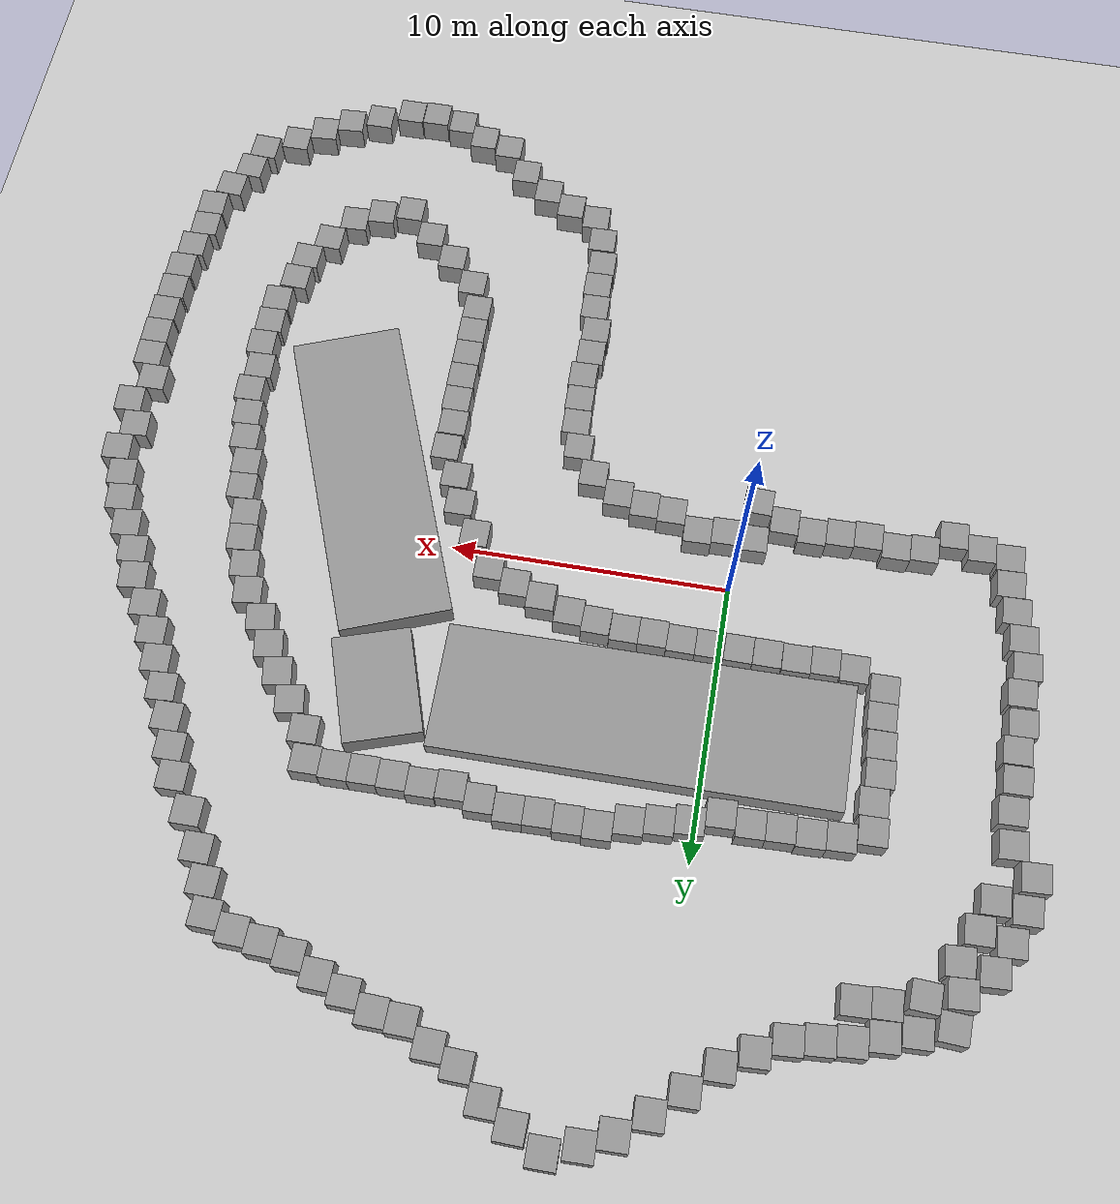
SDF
<sdf version="1.7">
 <world name="default">
  <light name="sun" type="directional">
   <pose>0 0 10 0 -0 0</pose>
   <diffuse>0.8 0.8 0.8 1</diffuse>
   <specular>0.2 0.2 0.2 1</specular>
   <attenuation>
    <range>1000</range>
    <constant>0.9</constant>
    <linear>0.01</linear>
    <quadratic>0.001</quadratic>
   </attenuation>
   <direction>-0.5 0.1 -0.9</direction>
   <spot><inner_angle>0</inner_angle><outer_angle>0</outer_angle><falloff>0</falloff></spot>
  </light>
  <model name="ground_plane">
   <static>1</static>
   <link name="link">
    <collision name="collision">
     <geometry><plane><normal>0 0 1</normal><size>100 100</size></plane></geometry>
     <surface>
      <contact><collide_bitmask>65535</collide_bitmask></contact>
      <friction><ode><mu>100</mu><mu2>50</mu2></ode></friction>
     </surface>
    </collision>
    <visual name="visual">
     <cast_shadows>0</cast_shadows>
     <geometry><plane><normal>0 0 1</normal><size>100 100</size></plane></geometry>
     <material>
      <script><uri>file://media/materials/scripts/gazebo.material</uri><name>Gazebo/Grey</name></script>
     </material>
    </visual>
   </link>
  </model>
  <gravity>0 0 -9.8</gravity>
  <magnetic_field>6e-06 2.3e-05 -4.2e-05</magnetic_field>
  <atmosphere type="adiabatic"/>
  <physics type="ode">
   <max_step_size>0.001</max_step_size>
   <real_time_factor>1</real_time_factor>
   <real_time_update_rate>1000</real_time_update_rate>
  </physics>
  <scene><ambient>0.4 0.4 0.4 1</ambient><background>0.7 0.7 0.7 1</background><shadows>1</shadows></scene>
  <spherical_coordinates>
   <surface_model>EARTH_WGS84</surface_model>
   <latitude_deg>0</latitude_deg>
   <longitude_deg>0</longitude_deg>
   <elevation>0</elevation>
   <heading_deg>0</heading_deg>
  </spherical_coordinates>
  <model name="unit_box">
   <pose>-1.63061 2.48149 0.499995 -1e-05 -0 0.003924</pose>
   <link name="link">
    <inertial>
     <mass>1</mass>
     <inertia>
      <ixx>0.166667</ixx>
      <ixy>0</ixy>
      <ixz>0</ixz>
      <iyy>0.166667</iyy>
      <iyz>0</iyz>
      <izz>0.166667</izz>
     </inertia>
    </inertial>
    <collision name="collision"><geometry><box><size>1 1 1</size></box></geometry></collision>
    <visual name="visual">
     <geometry><box><size>1 1 1</size></box></geometry>
     <material>
      <script><name>Gazebo/Grey</name><uri>file://media/materials/scripts/gazebo.material</uri></script>
     </material>
    </visual>
   </link>
  </model>
  <model name="unit_box_0">
   <pose>-0.627473 2.48305 0.499995 -1e-05 -0 -0.002213</pose>
   <link name="link">
    <inertial>
     <mass>1</mass>
     <inertia>
      <ixx>0.166667</ixx>
      <ixy>0</ixy>
      <ixz>0</ixz>
      <iyy>0.166667</iyy>
      <iyz>0</iyz>
      <izz>0.166667</izz>
     </inertia>
    </inertial>
    <collision name="collision"><geometry><box><size>1 1 1</size></box></geometry></collision>
    <visual name="visual">
     <geometry><box><size>1 1 1</size></box></geometry>
     <material>
      <script><name>Gazebo/Grey</name><uri>file://media/materials/scripts/gazebo.material</uri></script>
     </material>
    </visual>
   </link>
  </model>
  <model name="unit_box_1">
   <pose>0.372526 2.48136 0.499995 -1e-05 -0 -0.002213</pose>
   <link name="link">
    <inertial>
     <mass>1</mass>
     <inertia>
      <ixx>0.166667</ixx>
      <ixy>0</ixy>
      <ixz>0</ixz>
      <iyy>0.166667</iyy>
      <iyz>0</iyz>
      <izz>0.166667</izz>
     </inertia>
    </inertial>
    <collision name="collision"><geometry><box><size>1 1 1</size></box></geometry></collision>
    <visual name="visual">
     <geometry><box><size>1 1 1</size></box></geometry>
     <material>
      <script><name>Gazebo/Grey</name><uri>file://media/materials/scripts/gazebo.material</uri></script>
     </material>
    </visual>
   </link>
  </model>
  <model name="unit_box_2">
   <pose>1.37261 2.47907 0.499995 1e-05 0 -0.002067</pose>
   <link name="link">
    <inertial>
     <mass>1</mass>
     <inertia>
      <ixx>0.166667</ixx>
      <ixy>0</ixy>
      <ixz>0</ixz>
      <iyy>0.166667</iyy>
      <iyz>0</iyz>
      <izz>0.166667</izz>
     </inertia>
    </inertial>
    <collision name="collision"><geometry><box><size>1 1 1</size></box></geometry></collision>
    <visual name="visual">
     <geometry><box><size>1 1 1</size></box></geometry>
     <material>
      <script><name>Gazebo/Grey</name><uri>file://media/materials/scripts/gazebo.material</uri></script>
     </material>
    </visual>
   </link>
  </model>
  <model name="unit_box_3">
   <pose>2.37253 2.41079 0.499995 -1e-05 -0 -0.001964</pose>
   <link name="link">
    <inertial>
     <mass>1</mass>
     <inertia>
      <ixx>0.166667</ixx>
      <ixy>0</ixy>
      <ixz>0</ixz>
      <iyy>0.166667</iyy>
      <iyz>0</iyz>
      <izz>0.166667</izz>
     </inertia>
    </inertial>
    <collision name="collision"><geometry><box><size>1 1 1</size></box></geometry></collision>
    <visual name="visual">
     <geometry><box><size>1 1 1</size></box></geometry>
     <material>
      <script><name>Gazebo/Grey</name><uri>file://media/materials/scripts/gazebo.material</uri></script>
     </material>
    </visual>
   </link>
  </model>
  <model name="unit_box_4">
   <pose>3.37256 2.41731 0.499995 -0 -1e-05 -0.001944</pose>
   <link name="link">
    <inertial>
     <mass>1</mass>
     <inertia>
      <ixx>0.166667</ixx>
      <ixy>0</ixy>
      <ixz>0</ixz>
      <iyy>0.166667</iyy>
      <iyz>0</iyz>
      <izz>0.166667</izz>
     </inertia>
    </inertial>
    <collision name="collision"><geometry><box><size>1 1 1</size></box></geometry></collision>
    <visual name="visual">
     <geometry><box><size>1 1 1</size></box></geometry>
     <material>
      <script><name>Gazebo/Grey</name><uri>file://media/materials/scripts/gazebo.material</uri></script>
     </material>
    </visual>
   </link>
  </model>
  <model name="unit_box_5">
   <pose>-1.63227 -2.63168 0.499995 0 -1e-05 -0.008028</pose>
   <link name="link">
    <inertial>
     <mass>1</mass>
     <inertia>
      <ixx>0.166667</ixx>
      <ixy>0</ixy>
      <ixz>0</ixz>
      <iyy>0.166667</iyy>
      <iyz>0</iyz>
      <izz>0.166667</izz>
     </inertia>
    </inertial>
    <collision name="collision"><geometry><box><size>1 1 1</size></box></geometry></collision>
    <visual name="visual">
     <geometry><box><size>1 1 1</size></box></geometry>
     <material>
      <script><name>Gazebo/Grey</name><uri>file://media/materials/scripts/gazebo.material</uri></script>
     </material>
    </visual>
   </link>
  </model>
  <model name="unit_box_6">
   <pose>-2.63557 2.50705 0.499995 1e-05 0 0.012705</pose>
   <link name="link">
    <inertial>
     <mass>1</mass>
     <inertia>
      <ixx>0.166667</ixx>
      <ixy>0</ixy>
      <ixz>0</ixz>
      <iyy>0.166667</iyy>
      <iyz>0</iyz>
      <izz>0.166667</izz>
     </inertia>
    </inertial>
    <collision name="collision"><geometry><box><size>1 1 1</size></box></geometry></collision>
    <visual name="visual">
     <geometry><box><size>1 1 1</size></box></geometry>
     <material>
      <script><name>Gazebo/Grey</name><uri>file://media/materials/scripts/gazebo.material</uri></script>
     </material>
    </visual>
   </link>
  </model>
  <model name="unit_box_7">
   <pose>-3.63503 2.45257 0.499995 1e-05 -0 0.012608</pose>
   <link name="link">
    <inertial>
     <mass>1</mass>
     <inertia>
      <ixx>0.166667</ixx>
      <ixy>0</ixy>
      <ixz>0</ixz>
      <iyy>0.166667</iyy>
      <iyz>0</iyz>
      <izz>0.166667</izz>
     </inertia>
    </inertial>
    <collision name="collision"><geometry><box><size>1 1 1</size></box></geometry></collision>
    <visual name="visual">
     <geometry><box><size>1 1 1</size></box></geometry>
     <material>
      <script><name>Gazebo/Grey</name><uri>file://media/materials/scripts/gazebo.material</uri></script>
     </material>
    </visual>
   </link>
  </model>
  <model name="unit_box_8">
   <pose>-4.63657 2.54261 0.499995 1e-05 0 0.011882</pose>
   <link name="link">
    <inertial>
     <mass>1</mass>
     <inertia>
      <ixx>0.166667</ixx>
      <ixy>0</ixy>
      <ixz>0</ixz>
      <iyy>0.166667</iyy>
      <iyz>0</iyz>
      <izz>0.166667</izz>
     </inertia>
    </inertial>
    <collision name="collision"><geometry><box><size>1 1 1</size></box></geometry></collision>
    <visual name="visual">
     <geometry><box><size>1 1 1</size></box></geometry>
     <material>
      <script><name>Gazebo/Grey</name><uri>file://media/materials/scripts/gazebo.material</uri></script>
     </material>
    </visual>
   </link>
  </model>
  <model name="unit_box_9">
   <pose>-2.63745 -2.38464 0.499995 0 1e-05 0.002465</pose>
   <link name="link">
    <inertial>
     <mass>1</mass>
     <inertia>
      <ixx>0.166667</ixx>
      <ixy>0</ixy>
      <ixz>0</ixz>
      <iyy>0.166667</iyy>
      <iyz>0</iyz>
      <izz>0.166667</izz>
     </inertia>
    </inertial>
    <collision name="collision"><geometry><box><size>1 1 1</size></box></geometry></collision>
    <visual name="visual">
     <geometry><box><size>1 1 1</size></box></geometry>
     <material>
      <script><name>Gazebo/Grey</name><uri>file://media/materials/scripts/gazebo.material</uri></script>
     </material>
    </visual>
   </link>
  </model>
  <model name="unit_box_10">
   <pose>-3.63746 -2.49022 0.499995 -0 1e-05 0.003056</pose>
   <link name="link">
    <inertial>
     <mass>1</mass>
     <inertia>
      <ixx>0.166667</ixx>
      <ixy>0</ixy>
      <ixz>0</ixz>
      <iyy>0.166667</iyy>
      <iyz>0</iyz>
      <izz>0.166667</izz>
     </inertia>
    </inertial>
    <collision name="collision"><geometry><box><size>1 1 1</size></box></geometry></collision>
    <visual name="visual">
     <geometry><box><size>1 1 1</size></box></geometry>
     <material>
      <script><name>Gazebo/Grey</name><uri>file://media/materials/scripts/gazebo.material</uri></script>
     </material>
    </visual>
   </link>
  </model>
  <model name="unit_box_11">
   <pose>-0.613583 -1.75545 0.499995 -1e-05 0 0.017502</pose>
   <link name="link">
    <inertial>
     <mass>1</mass>
     <inertia>
      <ixx>0.166667</ixx>
      <ixy>0</ixy>
      <ixz>0</ixz>
      <iyy>0.166667</iyy>
      <iyz>0</iyz>
      <izz>0.166667</izz>
     </inertia>
    </inertial>
    <collision name="collision"><geometry><box><size>1 1 1</size></box></geometry></collision>
    <visual name="visual">
     <geometry><box><size>1 1 1</size></box></geometry>
     <material>
      <script><name>Gazebo/Grey</name><uri>file://media/materials/scripts/gazebo.material</uri></script>
     </material>
    </visual>
   </link>
  </model>
  <model name="unit_box_12">
   <pose>0.388432 -1.86075 0.499995 -0 -9e-06 0.017468</pose>
   <link name="link">
    <inertial>
     <mass>1</mass>
     <inertia>
      <ixx>0.166667</ixx>
      <ixy>0</ixy>
      <ixz>0</ixz>
      <iyy>0.166667</iyy>
      <iyz>0</iyz>
      <izz>0.166667</izz>
     </inertia>
    </inertial>
    <collision name="collision"><geometry><box><size>1 1 1</size></box></geometry></collision>
    <visual name="visual">
     <geometry><box><size>1 1 1</size></box></geometry>
     <material>
      <script><name>Gazebo/Grey</name><uri>file://media/materials/scripts/gazebo.material</uri></script>
     </material>
    </visual>
   </link>
  </model>
  <model name="unit_box_13">
   <pose>1.38661 -1.74674 0.499995 0 1e-05 0.017466</pose>
   <link name="link">
    <inertial>
     <mass>1</mass>
     <inertia>
      <ixx>0.166667</ixx>
      <ixy>0</ixy>
      <ixz>0</ixz>
      <iyy>0.166667</iyy>
      <iyz>0</iyz>
      <izz>0.166667</izz>
     </inertia>
    </inertial>
    <collision name="collision"><geometry><box><size>1 1 1</size></box></geometry></collision>
    <visual name="visual">
     <geometry><box><size>1 1 1</size></box></geometry>
     <material>
      <script><name>Gazebo/Grey</name><uri>file://media/materials/scripts/gazebo.material</uri></script>
     </material>
    </visual>
   </link>
  </model>
  <model name="unit_box_14">
   <pose>2.39599 -2.35306 0.499995 0 1e-05 0.006255</pose>
   <link name="link">
    <inertial>
     <mass>1</mass>
     <inertia>
      <ixx>0.166667</ixx>
      <ixy>0</ixy>
      <ixz>0</ixz>
      <iyy>0.166667</iyy>
      <iyz>0</iyz>
      <izz>0.166667</izz>
     </inertia>
    </inertial>
    <collision name="collision"><geometry><box><size>1 1 1</size></box></geometry></collision>
    <visual name="visual">
     <geometry><box><size>1 1 1</size></box></geometry>
     <material>
      <script><name>Gazebo/Grey</name><uri>file://media/materials/scripts/gazebo.material</uri></script>
     </material>
    </visual>
   </link>
  </model>
  <model name="unit_box_15">
   <pose>3.39655 -2.43483 0.499995 1e-05 0 0.00622</pose>
   <link name="link">
    <inertial>
     <mass>1</mass>
     <inertia>
      <ixx>0.166667</ixx>
      <ixy>0</ixy>
      <ixz>0</ixz>
      <iyy>0.166667</iyy>
      <iyz>0</iyz>
      <izz>0.166667</izz>
     </inertia>
    </inertial>
    <collision name="collision"><geometry><box><size>1 1 1</size></box></geometry></collision>
    <visual name="visual">
     <geometry><box><size>1 1 1</size></box></geometry>
     <material>
      <script><name>Gazebo/Grey</name><uri>file://media/materials/scripts/gazebo.material</uri></script>
     </material>
    </visual>
   </link>
  </model>
  <model name="unit_box_16">
   <pose>4.39824 -2.70245 0.499995 1e-05 0 0.00622</pose>
   <link name="link">
    <inertial>
     <mass>1</mass>
     <inertia>
      <ixx>0.166667</ixx>
      <ixy>0</ixy>
      <ixz>0</ixz>
      <iyy>0.166667</iyy>
      <iyz>0</iyz>
      <izz>0.166667</izz>
     </inertia>
    </inertial>
    <collision name="collision"><geometry><box><size>1 1 1</size></box></geometry></collision>
    <visual name="visual">
     <geometry><box><size>1 1 1</size></box></geometry>
     <material>
      <script><name>Gazebo/Grey</name><uri>file://media/materials/scripts/gazebo.material</uri></script>
     </material>
    </visual>
   </link>
  </model>
  <model name="unit_box_17">
   <pose>5.40236 -3.34784 0.499995 -0 1e-05 0.006361</pose>
   <link name="link">
    <inertial>
     <mass>1</mass>
     <inertia>
      <ixx>0.166667</ixx>
      <ixy>0</ixy>
      <ixz>0</ixz>
      <iyy>0.166667</iyy>
      <iyz>0</iyz>
      <izz>0.166667</izz>
     </inertia>
    </inertial>
    <collision name="collision"><geometry><box><size>1 1 1</size></box></geometry></collision>
    <visual name="visual">
     <geometry><box><size>1 1 1</size></box></geometry>
     <material>
      <script><name>Gazebo/Grey</name><uri>file://media/materials/scripts/gazebo.material</uri></script>
     </material>
    </visual>
   </link>
  </model>
  <model name="unit_box_18">
   <pose>6.11714 -4.34221 0.499995 0 -1e-05 0.011712</pose>
   <link name="link">
    <inertial>
     <mass>1</mass>
     <inertia>
      <ixx>0.166667</ixx>
      <ixy>0</ixy>
      <ixz>0</ixz>
      <iyy>0.166667</iyy>
      <iyz>0</iyz>
      <izz>0.166667</izz>
     </inertia>
    </inertial>
    <collision name="collision"><geometry><box><size>1 1 1</size></box></geometry></collision>
    <visual name="visual">
     <geometry><box><size>1 1 1</size></box></geometry>
     <material>
      <script><name>Gazebo/Grey</name><uri>file://media/materials/scripts/gazebo.material</uri></script>
     </material>
    </visual>
   </link>
  </model>
  <model name="unit_box_19">
   <pose>6.3639 -5.33969 0.499995 0 1e-05 0.011886</pose>
   <link name="link">
    <inertial>
     <mass>1</mass>
     <inertia>
      <ixx>0.166667</ixx>
      <ixy>0</ixy>
      <ixz>0</ixz>
      <iyy>0.166667</iyy>
      <iyz>0</iyz>
      <izz>0.166667</izz>
     </inertia>
    </inertial>
    <collision name="collision"><geometry><box><size>1 1 1</size></box></geometry></collision>
    <visual name="visual">
     <geometry><box><size>1 1 1</size></box></geometry>
     <material>
      <script><name>Gazebo/Grey</name><uri>file://media/materials/scripts/gazebo.material</uri></script>
     </material>
    </visual>
   </link>
  </model>
  <model name="unit_box_20">
   <pose>4.38108 2.28355 0.499995 -1e-05 -0 -0.015499</pose>
   <link name="link">
    <inertial>
     <mass>1</mass>
     <inertia>
      <ixx>0.166667</ixx>
      <ixy>0</ixy>
      <ixz>0</ixz>
      <iyy>0.166667</iyy>
      <iyz>0</iyz>
      <izz>0.166667</izz>
     </inertia>
    </inertial>
    <collision name="collision"><geometry><box><size>1 1 1</size></box></geometry></collision>
    <visual name="visual">
     <geometry><box><size>1 1 1</size></box></geometry>
     <material>
      <script><name>Gazebo/Grey</name><uri>file://media/materials/scripts/gazebo.material</uri></script>
     </material>
    </visual>
   </link>
  </model>
  <model name="unit_box_21">
   <pose>5.37842 2.09653 0.499995 -1e-05 -0 -0.0155</pose>
   <link name="link">
    <inertial>
     <mass>1</mass>
     <inertia>
      <ixx>0.166667</ixx>
      <ixy>0</ixy>
      <ixz>0</ixz>
      <iyy>0.166667</iyy>
      <iyz>0</iyz>
      <izz>0.166667</izz>
     </inertia>
    </inertial>
    <collision name="collision"><geometry><box><size>1 1 1</size></box></geometry></collision>
    <visual name="visual">
     <geometry><box><size>1 1 1</size></box></geometry>
     <material>
      <script><name>Gazebo/Grey</name><uri>file://media/materials/scripts/gazebo.material</uri></script>
     </material>
    </visual>
   </link>
  </model>
  <model name="unit_box_22">
   <pose>6.44585 1.71084 0.499995 0 1e-05 5e-06</pose>
   <link name="link">
    <inertial>
     <mass>1</mass>
     <inertia>
      <ixx>0.166667</ixx>
      <ixy>0</ixy>
      <ixz>0</ixz>
      <iyy>0.166667</iyy>
      <iyz>0</iyz>
      <izz>0.166667</izz>
     </inertia>
    </inertial>
    <collision name="collision"><geometry><box><size>1 1 1</size></box></geometry></collision>
    <visual name="visual">
     <geometry><box><size>1 1 1</size></box></geometry>
     <material>
      <script><name>Gazebo/Grey</name><uri>file://media/materials/scripts/gazebo.material</uri></script>
     </material>
    </visual>
   </link>
  </model>
  <model name="unit_box_23">
   <pose>7.44649 1.36321 0.499995 -1e-05 -0 5e-06</pose>
   <link name="link">
    <inertial>
     <mass>1</mass>
     <inertia>
      <ixx>0.166667</ixx>
      <ixy>0</ixy>
      <ixz>0</ixz>
      <iyy>0.166667</iyy>
      <iyz>0</iyz>
      <izz>0.166667</izz>
     </inertia>
    </inertial>
    <collision name="collision"><geometry><box><size>1 1 1</size></box></geometry></collision>
    <visual name="visual">
     <geometry><box><size>1 1 1</size></box></geometry>
     <material>
      <script><name>Gazebo/Grey</name><uri>file://media/materials/scripts/gazebo.material</uri></script>
     </material>
    </visual>
   </link>
  </model>
  <model name="unit_box_24">
   <pose>8.44685 0.885138 0.499995 0 1e-05 5e-06</pose>
   <link name="link">
    <inertial>
     <mass>1</mass>
     <inertia>
      <ixx>0.166667</ixx>
      <ixy>0</ixy>
      <ixz>0</ixz>
      <iyy>0.166667</iyy>
      <iyz>0</iyz>
      <izz>0.166667</izz>
     </inertia>
    </inertial>
    <collision name="collision"><geometry><box><size>1 1 1</size></box></geometry></collision>
    <visual name="visual">
     <geometry><box><size>1 1 1</size></box></geometry>
     <material>
      <script><name>Gazebo/Grey</name><uri>file://media/materials/scripts/gazebo.material</uri></script>
     </material>
    </visual>
   </link>
  </model>
  <model name="unit_box_25">
   <pose>9.18635 -0.29044 0.499995 -1e-05 -0 5e-06</pose>
   <link name="link">
    <inertial>
     <mass>1</mass>
     <inertia>
      <ixx>0.166667</ixx>
      <ixy>0</ixy>
      <ixz>0</ixz>
      <iyy>0.166667</iyy>
      <iyz>0</iyz>
      <izz>0.166667</izz>
     </inertia>
    </inertial>
    <collision name="collision"><geometry><box><size>1 1 1</size></box></geometry></collision>
    <visual name="visual">
     <geometry><box><size>1 1 1</size></box></geometry>
     <material>
      <script><name>Gazebo/Grey</name><uri>file://media/materials/scripts/gazebo.material</uri></script>
     </material>
    </visual>
   </link>
  </model>
  <model name="unit_box_26">
   <pose>9.95454 -1.40481 0.499995 1e-05 -0 0.004582</pose>
   <link name="link">
    <inertial>
     <mass>1</mass>
     <inertia>
      <ixx>0.166667</ixx>
      <ixy>0</ixy>
      <ixz>0</ixz>
      <iyy>0.166667</iyy>
      <iyz>0</iyz>
      <izz>0.166667</izz>
     </inertia>
    </inertial>
    <collision name="collision"><geometry><box><size>1 1 1</size></box></geometry></collision>
    <visual name="visual">
     <geometry><box><size>1 1 1</size></box></geometry>
     <material>
      <script><name>Gazebo/Grey</name><uri>file://media/materials/scripts/gazebo.material</uri></script>
     </material>
    </visual>
   </link>
  </model>
  <model name="unit_box_27">
   <pose>10.305 -2.44806 0.499995 -1e-05 -0 5e-06</pose>
   <link name="link">
    <inertial>
     <mass>1</mass>
     <inertia>
      <ixx>0.166667</ixx>
      <ixy>0</ixy>
      <ixz>0</ixz>
      <iyy>0.166667</iyy>
      <iyz>0</iyz>
      <izz>0.166667</izz>
     </inertia>
    </inertial>
    <collision name="collision"><geometry><box><size>1 1 1</size></box></geometry></collision>
    <visual name="visual">
     <geometry><box><size>1 1 1</size></box></geometry>
     <material>
      <script><name>Gazebo/Grey</name><uri>file://media/materials/scripts/gazebo.material</uri></script>
     </material>
    </visual>
   </link>
  </model>
  <model name="unit_box_28">
   <pose>10.8726 -3.51527 0.499995 -1e-05 -0 -5e-06</pose>
   <link name="link">
    <inertial>
     <mass>1</mass>
     <inertia>
      <ixx>0.166667</ixx>
      <ixy>0</ixy>
      <ixz>0</ixz>
      <iyy>0.166667</iyy>
      <iyz>0</iyz>
      <izz>0.166667</izz>
     </inertia>
    </inertial>
    <collision name="collision"><geometry><box><size>1 1 1</size></box></geometry></collision>
    <visual name="visual">
     <geometry><box><size>1 1 1</size></box></geometry>
     <material>
      <script><name>Gazebo/Grey</name><uri>file://media/materials/scripts/gazebo.material</uri></script>
     </material>
    </visual>
   </link>
  </model>
  <model name="unit_box_29">
   <pose>10.8241 -4.54943 0.499995 -1e-05 -0 0.000273</pose>
   <link name="link">
    <inertial>
     <mass>1</mass>
     <inertia>
      <ixx>0.166667</ixx>
      <ixy>0</ixy>
      <ixz>0</ixz>
      <iyy>0.166667</iyy>
      <iyz>0</iyz>
      <izz>0.166667</izz>
     </inertia>
    </inertial>
    <collision name="collision"><geometry><box><size>1 1 1</size></box></geometry></collision>
    <visual name="visual">
     <geometry><box><size>1 1 1</size></box></geometry>
     <material>
      <script><name>Gazebo/Grey</name><uri>file://media/materials/scripts/gazebo.material</uri></script>
     </material>
    </visual>
   </link>
  </model>
  <model name="unit_box_30">
   <pose>10.8797 -5.54946 0.499995 -1e-05 0 0.00022</pose>
   <link name="link">
    <inertial>
     <mass>1</mass>
     <inertia>
      <ixx>0.166667</ixx>
      <ixy>0</ixy>
      <ixz>0</ixz>
      <iyy>0.166667</iyy>
      <iyz>0</iyz>
      <izz>0.166667</izz>
     </inertia>
    </inertial>
    <collision name="collision"><geometry><box><size>1 1 1</size></box></geometry></collision>
    <visual name="visual">
     <geometry><box><size>1 1 1</size></box></geometry>
     <material>
      <script><name>Gazebo/Grey</name><uri>file://media/materials/scripts/gazebo.material</uri></script>
     </material>
    </visual>
   </link>
  </model>
  <model name="unit_box_31">
   <pose>6.41406 -6.33969 0.499995 0 1e-05 0.012971</pose>
   <link name="link">
    <inertial>
     <mass>1</mass>
     <inertia>
      <ixx>0.166667</ixx>
      <ixy>0</ixy>
      <ixz>0</ixz>
      <iyy>0.166667</iyy>
      <iyz>0</iyz>
      <izz>0.166667</izz>
     </inertia>
    </inertial>
    <collision name="collision"><geometry><box><size>1 1 1</size></box></geometry></collision>
    <visual name="visual">
     <geometry><box><size>1 1 1</size></box></geometry>
     <material>
      <script><name>Gazebo/Grey</name><uri>file://media/materials/scripts/gazebo.material</uri></script>
     </material>
    </visual>
   </link>
  </model>
  <model name="unit_box_32">
   <pose>10.8891 -6.54951 0.499995 0 1e-05 0.00017</pose>
   <link name="link">
    <inertial>
     <mass>1</mass>
     <inertia>
      <ixx>0.166667</ixx>
      <ixy>0</ixy>
      <ixz>0</ixz>
      <iyy>0.166667</iyy>
      <iyz>0</iyz>
      <izz>0.166667</izz>
     </inertia>
    </inertial>
    <collision name="collision"><geometry><box><size>1 1 1</size></box></geometry></collision>
    <visual name="visual">
     <geometry><box><size>1 1 1</size></box></geometry>
     <material>
      <script><name>Gazebo/Grey</name><uri>file://media/materials/scripts/gazebo.material</uri></script>
     </material>
    </visual>
   </link>
  </model>
  <model name="unit_box_33">
   <pose>6.46012 -7.33918 0.5 0 -0 0.012974</pose>
   <link name="link">
    <inertial>
     <mass>1</mass>
     <inertia>
      <ixx>0.166667</ixx>
      <ixy>0</ixy>
      <ixz>0</ixz>
      <iyy>0.166667</iyy>
      <iyz>0</iyz>
      <izz>0.166667</izz>
     </inertia>
    </inertial>
    <collision name="collision"><geometry><box><size>1 1 1</size></box></geometry></collision>
    <visual name="visual">
     <geometry><box><size>1 1 1</size></box></geometry>
     <material>
      <script><name>Gazebo/Grey</name><uri>file://media/materials/scripts/gazebo.material</uri></script>
     </material>
    </visual>
   </link>
  </model>
  <model name="unit_box_32_clone">
   <pose>6.33219 -8.3411 0.5 0 -0 0.013303</pose>
   <link name="link">
    <inertial>
     <mass>1</mass>
     <inertia>
      <ixx>0.166667</ixx>
      <ixy>0</ixy>
      <ixz>0</ixz>
      <iyy>0.166667</iyy>
      <iyz>0</iyz>
      <izz>0.166667</izz>
     </inertia>
    </inertial>
    <collision name="collision"><geometry><box><size>1 1 1</size></box></geometry></collision>
    <visual name="visual">
     <geometry><box><size>1 1 1</size></box></geometry>
     <material>
      <script><name>Gazebo/Grey</name><uri>file://media/materials/scripts/gazebo.material</uri></script>
     </material>
    </visual>
   </link>
  </model>
  <model name="unit_box_32_clone_0">
   <pose>10.8828 -7.54992 0.499995 -1e-05 -0 -0.000395</pose>
   <link name="link">
    <inertial>
     <mass>1</mass>
     <inertia>
      <ixx>0.166667</ixx>
      <ixy>0</ixy>
      <ixz>0</ixz>
      <iyy>0.166667</iyy>
      <iyz>0</iyz>
      <izz>0.166667</izz>
     </inertia>
    </inertial>
    <collision name="collision"><geometry><box><size>1 1 1</size></box></geometry></collision>
    <visual name="visual">
     <geometry><box><size>1 1 1</size></box></geometry>
     <material>
      <script><name>Gazebo/Grey</name><uri>file://media/materials/scripts/gazebo.material</uri></script>
     </material>
    </visual>
   </link>
  </model>
  <model name="unit_box_32_clone_1">
   <pose>6.30855 -9.34159 0.499995 -0 -1e-05 0.013486</pose>
   <link name="link">
    <inertial>
     <mass>1</mass>
     <inertia>
      <ixx>0.166667</ixx>
      <ixy>0</ixy>
      <ixz>0</ixz>
      <iyy>0.166667</iyy>
      <iyz>0</iyz>
      <izz>0.166667</izz>
     </inertia>
    </inertial>
    <collision name="collision"><geometry><box><size>1 1 1</size></box></geometry></collision>
    <visual name="visual">
     <geometry><box><size>1 1 1</size></box></geometry>
     <material>
      <script><name>Gazebo/Grey</name><uri>file://media/materials/scripts/gazebo.material</uri></script>
     </material>
    </visual>
   </link>
  </model>
  <model name="unit_box_32_clone_2">
   <pose>6.49657 -10.3392 0.499995 -0 1e-05 0.013508</pose>
   <link name="link">
    <inertial>
     <mass>1</mass>
     <inertia>
      <ixx>0.166667</ixx>
      <ixy>0</ixy>
      <ixz>0</ixz>
      <iyy>0.166667</iyy>
      <iyz>0</iyz>
      <izz>0.166667</izz>
     </inertia>
    </inertial>
    <collision name="collision"><geometry><box><size>1 1 1</size></box></geometry></collision>
    <visual name="visual">
     <geometry><box><size>1 1 1</size></box></geometry>
     <material>
      <script><name>Gazebo/Grey</name><uri>file://media/materials/scripts/gazebo.material</uri></script>
     </material>
    </visual>
   </link>
  </model>
  <model name="unit_box_32_clone_3">
   <pose>10.8991 -8.55073 0.499995 0 -1e-05 -0.001861</pose>
   <link name="link">
    <inertial>
     <mass>1</mass>
     <inertia>
      <ixx>0.166667</ixx>
      <ixy>0</ixy>
      <ixz>0</ixz>
      <iyy>0.166667</iyy>
      <iyz>0</iyz>
      <izz>0.166667</izz>
     </inertia>
    </inertial>
    <collision name="collision"><geometry><box><size>1 1 1</size></box></geometry></collision>
    <visual name="visual">
     <geometry><box><size>1 1 1</size></box></geometry>
     <material>
      <script><name>Gazebo/Grey</name><uri>file://media/materials/scripts/gazebo.material</uri></script>
     </material>
    </visual>
   </link>
  </model>
  <model name="unit_box_32_clone_4">
   <pose>10.8972 -9.55127 0.499995 0 -1e-05 -0.002928</pose>
   <link name="link">
    <inertial>
     <mass>1</mass>
     <inertia>
      <ixx>0.166667</ixx>
      <ixy>0</ixy>
      <ixz>0</ixz>
      <iyy>0.166667</iyy>
      <iyz>0</iyz>
      <izz>0.166667</izz>
     </inertia>
    </inertial>
    <collision name="collision"><geometry><box><size>1 1 1</size></box></geometry></collision>
    <visual name="visual">
     <geometry><box><size>1 1 1</size></box></geometry>
     <material>
      <script><name>Gazebo/Grey</name><uri>file://media/materials/scripts/gazebo.material</uri></script>
     </material>
    </visual>
   </link>
  </model>
  <model name="unit_box_32_clone_5">
   <pose>6.55509 -11.3385 0.499995 0 1e-05 0.013501</pose>
   <link name="link">
    <inertial>
     <mass>1</mass>
     <inertia>
      <ixx>0.166667</ixx>
      <ixy>0</ixy>
      <ixz>0</ixz>
      <iyy>0.166667</iyy>
      <iyz>0</iyz>
      <izz>0.166667</izz>
     </inertia>
    </inertial>
    <collision name="collision"><geometry><box><size>1 1 1</size></box></geometry></collision>
    <visual name="visual">
     <geometry><box><size>1 1 1</size></box></geometry>
     <material>
      <script><name>Gazebo/Grey</name><uri>file://media/materials/scripts/gazebo.material</uri></script>
     </material>
    </visual>
   </link>
  </model>
  <model name="unit_box_32_clone_6">
   <pose>11.276 -10.6109 0.499995 0 1e-05 0.001319</pose>
   <link name="link">
    <inertial>
     <mass>1</mass>
     <inertia>
      <ixx>0.166667</ixx>
      <ixy>0</ixy>
      <ixz>0</ixz>
      <iyy>0.166667</iyy>
      <iyz>0</iyz>
      <izz>0.166667</izz>
     </inertia>
    </inertial>
    <collision name="collision"><geometry><box><size>1 1 1</size></box></geometry></collision>
    <visual name="visual">
     <geometry><box><size>1 1 1</size></box></geometry>
     <material>
      <script><name>Gazebo/Grey</name><uri>file://media/materials/scripts/gazebo.material</uri></script>
     </material>
    </visual>
   </link>
  </model>
  <model name="unit_box_32_clone_7">
   <pose>12.2553 -11.6331 0.499995 0 1e-05 0.001319</pose>
   <link name="link">
    <inertial>
     <mass>1</mass>
     <inertia>
      <ixx>0.166667</ixx>
      <ixy>0</ixy>
      <ixz>0</ixz>
      <iyy>0.166667</iyy>
      <iyz>0</iyz>
      <izz>0.166667</izz>
     </inertia>
    </inertial>
    <collision name="collision"><geometry><box><size>1 1 1</size></box></geometry></collision>
    <visual name="visual">
     <geometry><box><size>1 1 1</size></box></geometry>
     <material>
      <script><name>Gazebo/Grey</name><uri>file://media/materials/scripts/gazebo.material</uri></script>
     </material>
    </visual>
   </link>
  </model>
  <model name="unit_box_32_clone_8">
   <pose>13.2773 -12.5272 0.499995 0 1e-05 0.001319</pose>
   <link name="link">
    <inertial>
     <mass>1</mass>
     <inertia>
      <ixx>0.166667</ixx>
      <ixy>0</ixy>
      <ixz>0</ixz>
      <iyy>0.166667</iyy>
      <iyz>0</iyz>
      <izz>0.166667</izz>
     </inertia>
    </inertial>
    <collision name="collision"><geometry><box><size>1 1 1</size></box></geometry></collision>
    <visual name="visual">
     <geometry><box><size>1 1 1</size></box></geometry>
     <material>
      <script><name>Gazebo/Grey</name><uri>file://media/materials/scripts/gazebo.material</uri></script>
     </material>
    </visual>
   </link>
  </model>
  <model name="unit_box_32_clone_9">
   <pose>14.2987 -13.549 0.499995 0 1e-05 0.001319</pose>
   <link name="link">
    <inertial>
     <mass>1</mass>
     <inertia>
      <ixx>0.166667</ixx>
      <ixy>0</ixy>
      <ixz>0</ixz>
      <iyy>0.166667</iyy>
      <iyz>0</iyz>
      <izz>0.166667</izz>
     </inertia>
    </inertial>
    <collision name="collision"><geometry><box><size>1 1 1</size></box></geometry></collision>
    <visual name="visual">
     <geometry><box><size>1 1 1</size></box></geometry>
     <material>
      <script><name>Gazebo/Grey</name><uri>file://media/materials/scripts/gazebo.material</uri></script>
     </material>
    </visual>
   </link>
  </model>
  <model name="unit_box_32_clone_10">
   <pose>15.3803 -13.2281 0.499995 0 1e-05 0.040936</pose>
   <link name="link">
    <inertial>
     <mass>1</mass>
     <inertia>
      <ixx>0.166667</ixx>
      <ixy>0</ixy>
      <ixz>0</ixz>
      <iyy>0.166667</iyy>
      <iyz>0</iyz>
      <izz>0.166667</izz>
     </inertia>
    </inertial>
    <collision name="collision"><geometry><box><size>1 1 1</size></box></geometry></collision>
    <visual name="visual">
     <geometry><box><size>1 1 1</size></box></geometry>
     <material>
      <script><name>Gazebo/Grey</name><uri>file://media/materials/scripts/gazebo.material</uri></script>
     </material>
    </visual>
   </link>
  </model>
  <model name="unit_box_32_clone_11">
   <pose>16.3621 -12.7297 0.499995 0 1e-05 0.038196</pose>
   <link name="link">
    <inertial>
     <mass>1</mass>
     <inertia>
      <ixx>0.166667</ixx>
      <ixy>0</ixy>
      <ixz>0</ixz>
      <iyy>0.166667</iyy>
      <iyz>0</iyz>
      <izz>0.166667</izz>
     </inertia>
    </inertial>
    <collision name="collision"><geometry><box><size>1 1 1</size></box></geometry></collision>
    <visual name="visual">
     <geometry><box><size>1 1 1</size></box></geometry>
     <material>
      <script><name>Gazebo/Grey</name><uri>file://media/materials/scripts/gazebo.material</uri></script>
     </material>
    </visual>
   </link>
  </model>
  <model name="unit_box_32_clone_12">
   <pose>17.1342 -11.7208 0.5 0 0 -0.034855</pose>
   <link name="link">
    <inertial>
     <mass>1</mass>
     <inertia>
      <ixx>0.166667</ixx>
      <ixy>0</ixy>
      <ixz>0</ixz>
      <iyy>0.166667</iyy>
      <iyz>0</iyz>
      <izz>0.166667</izz>
     </inertia>
    </inertial>
    <collision name="collision"><geometry><box><size>1 1 1</size></box></geometry></collision>
    <visual name="visual">
     <geometry><box><size>1 1 1</size></box></geometry>
     <material>
      <script><name>Gazebo/Grey</name><uri>file://media/materials/scripts/gazebo.material</uri></script>
     </material>
    </visual>
   </link>
  </model>
  <model name="unit_box_32_clone_13">
   <pose>17.8095 -10.7409 0.499995 0 1e-05 -0.029256</pose>
   <link name="link">
    <inertial>
     <mass>1</mass>
     <inertia>
      <ixx>0.166667</ixx>
      <ixy>0</ixy>
      <ixz>0</ixz>
      <iyy>0.166667</iyy>
      <iyz>0</iyz>
      <izz>0.166667</izz>
     </inertia>
    </inertial>
    <collision name="collision"><geometry><box><size>1 1 1</size></box></geometry></collision>
    <visual name="visual">
     <geometry><box><size>1 1 1</size></box></geometry>
     <material>
      <script><name>Gazebo/Grey</name><uri>file://media/materials/scripts/gazebo.material</uri></script>
     </material>
    </visual>
   </link>
  </model>
  <model name="unit_box_32_clone_14">
   <pose>18.0046 -9.74616 0.499995 0 1e-05 -0.029233</pose>
   <link name="link">
    <inertial>
     <mass>1</mass>
     <inertia>
      <ixx>0.166667</ixx>
      <ixy>0</ixy>
      <ixz>0</ixz>
      <iyy>0.166667</iyy>
      <iyz>0</iyz>
      <izz>0.166667</izz>
     </inertia>
    </inertial>
    <collision name="collision"><geometry><box><size>1 1 1</size></box></geometry></collision>
    <visual name="visual">
     <geometry><box><size>1 1 1</size></box></geometry>
     <material>
      <script><name>Gazebo/Grey</name><uri>file://media/materials/scripts/gazebo.material</uri></script>
     </material>
    </visual>
   </link>
  </model>
  <model name="unit_box_32_clone_15">
   <pose>18.4737 -8.69085 0.499997 0 7e-06 0.02412</pose>
   <link name="link">
    <inertial>
     <mass>1</mass>
     <inertia>
      <ixx>0.166667</ixx>
      <ixy>0</ixy>
      <ixz>0</ixz>
      <iyy>0.166667</iyy>
      <iyz>0</iyz>
      <izz>0.166667</izz>
     </inertia>
    </inertial>
    <collision name="collision"><geometry><box><size>1 1 1</size></box></geometry></collision>
    <visual name="visual">
     <geometry><box><size>1 1 1</size></box></geometry>
     <material>
      <script><name>Gazebo/Grey</name><uri>file://media/materials/scripts/gazebo.material</uri></script>
     </material>
    </visual>
   </link>
  </model>
  <model name="unit_box_32_clone_16">
   <pose>18.5017 -7.68971 0.5 0 -0 0.024464</pose>
   <link name="link">
    <inertial>
     <mass>1</mass>
     <inertia>
      <ixx>0.166667</ixx>
      <ixy>0</ixy>
      <ixz>0</ixz>
      <iyy>0.166667</iyy>
      <iyz>0</iyz>
      <izz>0.166667</izz>
     </inertia>
    </inertial>
    <collision name="collision"><geometry><box><size>1 1 1</size></box></geometry></collision>
    <visual name="visual">
     <geometry><box><size>1 1 1</size></box></geometry>
     <material>
      <script><name>Gazebo/Grey</name><uri>file://media/materials/scripts/gazebo.material</uri></script>
     </material>
    </visual>
   </link>
  </model>
  <model name="unit_box_32_clone_17">
   <pose>18.5886 -6.68716 0.499995 0 -1e-05 0.024709</pose>
   <link name="link">
    <inertial>
     <mass>1</mass>
     <inertia>
      <ixx>0.166667</ixx>
      <ixy>0</ixy>
      <ixz>0</ixz>
      <iyy>0.166667</iyy>
      <iyz>0</iyz>
      <izz>0.166667</izz>
     </inertia>
    </inertial>
    <collision name="collision"><geometry><box><size>1 1 1</size></box></geometry></collision>
    <visual name="visual">
     <geometry><box><size>1 1 1</size></box></geometry>
     <material>
      <script><name>Gazebo/Grey</name><uri>file://media/materials/scripts/gazebo.material</uri></script>
     </material>
    </visual>
   </link>
  </model>
  <model name="unit_box_32_clone_18">
   <pose>18.4091 -5.69053 0.499995 0 -1e-05 0.026914</pose>
   <link name="link">
    <inertial>
     <mass>1</mass>
     <inertia>
      <ixx>0.166667</ixx>
      <ixy>0</ixy>
      <ixz>0</ixz>
      <iyy>0.166667</iyy>
      <iyz>0</iyz>
      <izz>0.166667</izz>
     </inertia>
    </inertial>
    <collision name="collision"><geometry><box><size>1 1 1</size></box></geometry></collision>
    <visual name="visual">
     <geometry><box><size>1 1 1</size></box></geometry>
     <material>
      <script><name>Gazebo/Grey</name><uri>file://media/materials/scripts/gazebo.material</uri></script>
     </material>
    </visual>
   </link>
  </model>
  <model name="unit_box_32_clone_19">
   <pose>18.5444 -4.6862 0.499995 -0 1e-05 0.027553</pose>
   <link name="link">
    <inertial>
     <mass>1</mass>
     <inertia>
      <ixx>0.166667</ixx>
      <ixy>0</ixy>
      <ixz>0</ixz>
      <iyy>0.166667</iyy>
      <iyz>0</iyz>
      <izz>0.166667</izz>
     </inertia>
    </inertial>
    <collision name="collision"><geometry><box><size>1 1 1</size></box></geometry></collision>
    <visual name="visual">
     <geometry><box><size>1 1 1</size></box></geometry>
     <material>
      <script><name>Gazebo/Grey</name><uri>file://media/materials/scripts/gazebo.material</uri></script>
     </material>
    </visual>
   </link>
  </model>
  <model name="unit_box_32_clone_20">
   <pose>18.3756 -3.68446 0.499995 -0 -1e-05 0.044092</pose>
   <link name="link">
    <inertial>
     <mass>1</mass>
     <inertia>
      <ixx>0.166667</ixx>
      <ixy>0</ixy>
      <ixz>0</ixz>
      <iyy>0.166667</iyy>
      <iyz>0</iyz>
      <izz>0.166667</izz>
     </inertia>
    </inertial>
    <collision name="collision"><geometry><box><size>1 1 1</size></box></geometry></collision>
    <visual name="visual">
     <geometry><box><size>1 1 1</size></box></geometry>
     <material>
      <script><name>Gazebo/Grey</name><uri>file://media/materials/scripts/gazebo.material</uri></script>
     </material>
    </visual>
   </link>
  </model>
  <model name="unit_box_32_clone_21">
   <pose>18.2038 -2.69101 0.499995 0 -1e-05 0.044246</pose>
   <link name="link">
    <inertial>
     <mass>1</mass>
     <inertia>
      <ixx>0.166667</ixx>
      <ixy>0</ixy>
      <ixz>0</ixz>
      <iyy>0.166667</iyy>
      <iyz>0</iyz>
      <izz>0.166667</izz>
     </inertia>
    </inertial>
    <collision name="collision"><geometry><box><size>1 1 1</size></box></geometry></collision>
    <visual name="visual">
     <geometry><box><size>1 1 1</size></box></geometry>
     <material>
      <script><name>Gazebo/Grey</name><uri>file://media/materials/scripts/gazebo.material</uri></script>
     </material>
    </visual>
   </link>
  </model>
  <model name="unit_box_32_clone_22">
   <pose>17.9148 -1.70228 0.5 0 -0 0.04637</pose>
   <link name="link">
    <inertial>
     <mass>1</mass>
     <inertia>
      <ixx>0.166667</ixx>
      <ixy>0</ixy>
      <ixz>0</ixz>
      <iyy>0.166667</iyy>
      <iyz>0</iyz>
      <izz>0.166667</izz>
     </inertia>
    </inertial>
    <collision name="collision"><geometry><box><size>1 1 1</size></box></geometry></collision>
    <visual name="visual">
     <geometry><box><size>1 1 1</size></box></geometry>
     <material>
      <script><name>Gazebo/Grey</name><uri>file://media/materials/scripts/gazebo.material</uri></script>
     </material>
    </visual>
   </link>
  </model>
  <model name="unit_box_32_clone_23">
   <pose>17.822 -0.705491 0.499995 -0 -1e-05 0.046421</pose>
   <link name="link">
    <inertial>
     <mass>1</mass>
     <inertia>
      <ixx>0.166667</ixx>
      <ixy>0</ixy>
      <ixz>0</ixz>
      <iyy>0.166667</iyy>
      <iyz>0</iyz>
      <izz>0.166667</izz>
     </inertia>
    </inertial>
    <collision name="collision"><geometry><box><size>1 1 1</size></box></geometry></collision>
    <visual name="visual">
     <geometry><box><size>1 1 1</size></box></geometry>
     <material>
      <script><name>Gazebo/Grey</name><uri>file://media/materials/scripts/gazebo.material</uri></script>
     </material>
    </visual>
   </link>
  </model>
  <model name="unit_box_32_clone_24">
   <pose>17.4264 0.282866 0.5 0 -0 0.081788</pose>
   <link name="link">
    <inertial>
     <mass>1</mass>
     <inertia>
      <ixx>0.166667</ixx>
      <ixy>0</ixy>
      <ixz>0</ixz>
      <iyy>0.166667</iyy>
      <iyz>0</iyz>
      <izz>0.166667</izz>
     </inertia>
    </inertial>
    <collision name="collision"><geometry><box><size>1 1 1</size></box></geometry></collision>
    <visual name="visual">
     <geometry><box><size>1 1 1</size></box></geometry>
     <material>
      <script><name>Gazebo/Grey</name><uri>file://media/materials/scripts/gazebo.material</uri></script>
     </material>
    </visual>
   </link>
  </model>
  <model name="unit_box_32_clone_25">
   <pose>17.3247 1.27792 0.5 0 -0 0.08186</pose>
   <link name="link">
    <inertial>
     <mass>1</mass>
     <inertia>
      <ixx>0.166667</ixx>
      <ixy>0</ixy>
      <ixz>0</ixz>
      <iyy>0.166667</iyy>
      <iyz>0</iyz>
      <izz>0.166667</izz>
     </inertia>
    </inertial>
    <collision name="collision"><geometry><box><size>1 1 1</size></box></geometry></collision>
    <visual name="visual">
     <geometry><box><size>1 1 1</size></box></geometry>
     <material>
      <script><name>Gazebo/Grey</name><uri>file://media/materials/scripts/gazebo.material</uri></script>
     </material>
    </visual>
   </link>
  </model>
  <model name="unit_box_32_clone_26">
   <pose>16.9722 2.26184 0.499995 -0 1e-05 0.121367</pose>
   <link name="link">
    <inertial>
     <mass>1</mass>
     <inertia>
      <ixx>0.166667</ixx>
      <ixy>0</ixy>
      <ixz>0</ixz>
      <iyy>0.166667</iyy>
      <iyz>0</iyz>
      <izz>0.166667</izz>
     </inertia>
    </inertial>
    <collision name="collision"><geometry><box><size>1 1 1</size></box></geometry></collision>
    <visual name="visual">
     <geometry><box><size>1 1 1</size></box></geometry>
     <material>
      <script><name>Gazebo/Grey</name><uri>file://media/materials/scripts/gazebo.material</uri></script>
     </material>
    </visual>
   </link>
  </model>
  <model name="unit_box_32_clone_27">
   <pose>16.6091 3.22503 0.5 0 -0 0.121596</pose>
   <link name="link">
    <inertial>
     <mass>1</mass>
     <inertia>
      <ixx>0.166667</ixx>
      <ixy>0</ixy>
      <ixz>0</ixz>
      <iyy>0.166667</iyy>
      <iyz>0</iyz>
      <izz>0.166667</izz>
     </inertia>
    </inertial>
    <collision name="collision"><geometry><box><size>1 1 1</size></box></geometry></collision>
    <visual name="visual">
     <geometry><box><size>1 1 1</size></box></geometry>
     <material>
      <script><name>Gazebo/Grey</name><uri>file://media/materials/scripts/gazebo.material</uri></script>
     </material>
    </visual>
   </link>
  </model>
  <model name="unit_box_32_clone_28">
   <pose>15.9248 4.1459 0.5 0 -0 0.175625</pose>
   <link name="link">
    <inertial>
     <mass>1</mass>
     <inertia>
      <ixx>0.166667</ixx>
      <ixy>0</ixy>
      <ixz>0</ixz>
      <iyy>0.166667</iyy>
      <iyz>0</iyz>
      <izz>0.166667</izz>
     </inertia>
    </inertial>
    <collision name="collision"><geometry><box><size>1 1 1</size></box></geometry></collision>
    <visual name="visual">
     <geometry><box><size>1 1 1</size></box></geometry>
     <material>
      <script><name>Gazebo/Grey</name><uri>file://media/materials/scripts/gazebo.material</uri></script>
     </material>
    </visual>
   </link>
  </model>
  <model name="unit_box_32_clone_29">
   <pose>15.4032 5.06902 0.499995 1e-05 -0 0.175627</pose>
   <link name="link">
    <inertial>
     <mass>1</mass>
     <inertia>
      <ixx>0.166667</ixx>
      <ixy>0</ixy>
      <ixz>0</ixz>
      <iyy>0.166667</iyy>
      <iyz>0</iyz>
      <izz>0.166667</izz>
     </inertia>
    </inertial>
    <collision name="collision"><geometry><box><size>1 1 1</size></box></geometry></collision>
    <visual name="visual">
     <geometry><box><size>1 1 1</size></box></geometry>
     <material>
      <script><name>Gazebo/Grey</name><uri>file://media/materials/scripts/gazebo.material</uri></script>
     </material>
    </visual>
   </link>
  </model>
  <model name="unit_box_32_clone_30">
   <pose>14.8669 5.98949 0.499995 1e-05 -0 0.175604</pose>
   <link name="link">
    <inertial>
     <mass>1</mass>
     <inertia>
      <ixx>0.166667</ixx>
      <ixy>0</ixy>
      <ixz>0</ixz>
      <iyy>0.166667</iyy>
      <iyz>0</iyz>
      <izz>0.166667</izz>
     </inertia>
    </inertial>
    <collision name="collision"><geometry><box><size>1 1 1</size></box></geometry></collision>
    <visual name="visual">
     <geometry><box><size>1 1 1</size></box></geometry>
     <material>
      <script><name>Gazebo/Grey</name><uri>file://media/materials/scripts/gazebo.material</uri></script>
     </material>
    </visual>
   </link>
  </model>
  <model name="unit_box_32_clone_31">
   <pose>14.216 6.89907 0.499996 -9e-06 0 0.157062</pose>
   <link name="link">
    <inertial>
     <mass>1</mass>
     <inertia>
      <ixx>0.166667</ixx>
      <ixy>0</ixy>
      <ixz>0</ixz>
      <iyy>0.166667</iyy>
      <iyz>0</iyz>
      <izz>0.166667</izz>
     </inertia>
    </inertial>
    <collision name="collision"><geometry><box><size>1 1 1</size></box></geometry></collision>
    <visual name="visual">
     <geometry><box><size>1 1 1</size></box></geometry>
     <material>
      <script><name>Gazebo/Grey</name><uri>file://media/materials/scripts/gazebo.material</uri></script>
     </material>
    </visual>
   </link>
  </model>
  <model name="unit_box_32_clone_32">
   <pose>13.4893 7.85691 0.5 0 -0 0.029155</pose>
   <link name="link">
    <inertial>
     <mass>1</mass>
     <inertia>
      <ixx>0.166667</ixx>
      <ixy>0</ixy>
      <ixz>0</ixz>
      <iyy>0.166667</iyy>
      <iyz>0</iyz>
      <izz>0.166667</izz>
     </inertia>
    </inertial>
    <collision name="collision"><geometry><box><size>1 1 1</size></box></geometry></collision>
    <visual name="visual">
     <geometry><box><size>1 1 1</size></box></geometry>
     <material>
      <script><name>Gazebo/Grey</name><uri>file://media/materials/scripts/gazebo.material</uri></script>
     </material>
    </visual>
   </link>
  </model>
  <model name="unit_box_32_clone_33">
   <pose>13.1982 8.87655 0.499995 1e-05 -0 0.01535</pose>
   <link name="link">
    <inertial>
     <mass>1</mass>
     <inertia>
      <ixx>0.166667</ixx>
      <ixy>0</ixy>
      <ixz>0</ixz>
      <iyy>0.166667</iyy>
      <iyz>0</iyz>
      <izz>0.166667</izz>
     </inertia>
    </inertial>
    <collision name="collision"><geometry><box><size>1 1 1</size></box></geometry></collision>
    <visual name="visual">
     <geometry><box><size>1 1 1</size></box></geometry>
     <material>
      <script><name>Gazebo/Grey</name><uri>file://media/materials/scripts/gazebo.material</uri></script>
     </material>
    </visual>
   </link>
  </model>
  <model name="unit_box_32_clone_34">
   <pose>6.54786 -12.3387 0.499995 1e-05 -0 0.013521</pose>
   <link name="link">
    <inertial>
     <mass>1</mass>
     <inertia>
      <ixx>0.166667</ixx>
      <ixy>0</ixy>
      <ixz>0</ixz>
      <iyy>0.166667</iyy>
      <iyz>0</iyz>
      <izz>0.166667</izz>
     </inertia>
    </inertial>
    <collision name="collision"><geometry><box><size>1 1 1</size></box></geometry></collision>
    <visual name="visual">
     <geometry><box><size>1 1 1</size></box></geometry>
     <material>
      <script><name>Gazebo/Grey</name><uri>file://media/materials/scripts/gazebo.material</uri></script>
     </material>
    </visual>
   </link>
  </model>
  <model name="unit_box_32_clone_35">
   <pose>6.70579 -13.3841 0.5 0 -0 0.026314</pose>
   <link name="link">
    <inertial>
     <mass>1</mass>
     <inertia>
      <ixx>0.166667</ixx>
      <ixy>0</ixy>
      <ixz>0</ixz>
      <iyy>0.166667</iyy>
      <iyz>0</iyz>
      <izz>0.166667</izz>
     </inertia>
    </inertial>
    <collision name="collision"><geometry><box><size>1 1 1</size></box></geometry></collision>
    <visual name="visual">
     <geometry><box><size>1 1 1</size></box></geometry>
     <material>
      <script><name>Gazebo/Grey</name><uri>file://media/materials/scripts/gazebo.material</uri></script>
     </material>
    </visual>
   </link>
  </model>
  <model name="unit_box_32_clone_36">
   <pose>7.11067 -14.374 0.499995 0 1e-05 0.026303</pose>
   <link name="link">
    <inertial>
     <mass>1</mass>
     <inertia>
      <ixx>0.166667</ixx>
      <ixy>0</ixy>
      <ixz>0</ixz>
      <iyy>0.166667</iyy>
      <iyz>0</iyz>
      <izz>0.166667</izz>
     </inertia>
    </inertial>
    <collision name="collision"><geometry><box><size>1 1 1</size></box></geometry></collision>
    <visual name="visual">
     <geometry><box><size>1 1 1</size></box></geometry>
     <material>
      <script><name>Gazebo/Grey</name><uri>file://media/materials/scripts/gazebo.material</uri></script>
     </material>
    </visual>
   </link>
  </model>
  <model name="unit_box_32_clone_37">
   <pose>8.15581 -14.7487 0.499995 -1e-05 -0 -0.004913</pose>
   <link name="link">
    <inertial>
     <mass>1</mass>
     <inertia>
      <ixx>0.166667</ixx>
      <ixy>0</ixy>
      <ixz>0</ixz>
      <iyy>0.166667</iyy>
      <iyz>0</iyz>
      <izz>0.166667</izz>
     </inertia>
    </inertial>
    <collision name="collision"><geometry><box><size>1 1 1</size></box></geometry></collision>
    <visual name="visual">
     <geometry><box><size>1 1 1</size></box></geometry>
     <material>
      <script><name>Gazebo/Grey</name><uri>file://media/materials/scripts/gazebo.material</uri></script>
     </material>
    </visual>
   </link>
  </model>
  <model name="unit_box_32_clone_38">
   <pose>9.15311 -15.3083 0.499995 0 -1e-05 -0.004922</pose>
   <link name="link">
    <inertial>
     <mass>1</mass>
     <inertia>
      <ixx>0.166667</ixx>
      <ixy>0</ixy>
      <ixz>0</ixz>
      <iyy>0.166667</iyy>
      <iyz>0</iyz>
      <izz>0.166667</izz>
     </inertia>
    </inertial>
    <collision name="collision"><geometry><box><size>1 1 1</size></box></geometry></collision>
    <visual name="visual">
     <geometry><box><size>1 1 1</size></box></geometry>
     <material>
      <script><name>Gazebo/Grey</name><uri>file://media/materials/scripts/gazebo.material</uri></script>
     </material>
    </visual>
   </link>
  </model>
  <model name="unit_box_32_clone_39">
   <pose>10.1652 -16.0712 0.499995 0 1e-05 0.001319</pose>
   <link name="link">
    <inertial>
     <mass>1</mass>
     <inertia>
      <ixx>0.166667</ixx>
      <ixy>0</ixy>
      <ixz>0</ixz>
      <iyy>0.166667</iyy>
      <iyz>0</iyz>
      <izz>0.166667</izz>
     </inertia>
    </inertial>
    <collision name="collision"><geometry><box><size>1 1 1</size></box></geometry></collision>
    <visual name="visual">
     <geometry><box><size>1 1 1</size></box></geometry>
     <material>
      <script><name>Gazebo/Grey</name><uri>file://media/materials/scripts/gazebo.material</uri></script>
     </material>
    </visual>
   </link>
  </model>
  <model name="unit_box_32_clone_40">
   <pose>11.0593 -17.1359 0.499995 0 1e-05 0.001319</pose>
   <link name="link">
    <inertial>
     <mass>1</mass>
     <inertia>
      <ixx>0.166667</ixx>
      <ixy>0</ixy>
      <ixz>0</ixz>
      <iyy>0.166667</iyy>
      <iyz>0</iyz>
      <izz>0.166667</izz>
     </inertia>
    </inertial>
    <collision name="collision"><geometry><box><size>1 1 1</size></box></geometry></collision>
    <visual name="visual">
     <geometry><box><size>1 1 1</size></box></geometry>
     <material>
      <script><name>Gazebo/Grey</name><uri>file://media/materials/scripts/gazebo.material</uri></script>
     </material>
    </visual>
   </link>
  </model>
  <model name="unit_box_32_clone_41">
   <pose>12.1154 -17.4308 0.499995 -0 1e-05 -0.005267</pose>
   <link name="link">
    <inertial>
     <mass>1</mass>
     <inertia>
      <ixx>0.166667</ixx>
      <ixy>0</ixy>
      <ixz>0</ixz>
      <iyy>0.166667</iyy>
      <iyz>0</iyz>
      <izz>0.166667</izz>
     </inertia>
    </inertial>
    <collision name="collision"><geometry><box><size>1 1 1</size></box></geometry></collision>
    <visual name="visual">
     <geometry><box><size>1 1 1</size></box></geometry>
     <material>
      <script><name>Gazebo/Grey</name><uri>file://media/materials/scripts/gazebo.material</uri></script>
     </material>
    </visual>
   </link>
  </model>
  <model name="unit_box_32_clone_42">
   <pose>13.1122 -18.0332 0.499995 0 1e-05 -0.005268</pose>
   <link name="link">
    <inertial>
     <mass>1</mass>
     <inertia>
      <ixx>0.166667</ixx>
      <ixy>0</ixy>
      <ixz>0</ixz>
      <iyy>0.166667</iyy>
      <iyz>0</iyz>
      <izz>0.166667</izz>
     </inertia>
    </inertial>
    <collision name="collision"><geometry><box><size>1 1 1</size></box></geometry></collision>
    <visual name="visual">
     <geometry><box><size>1 1 1</size></box></geometry>
     <material>
      <script><name>Gazebo/Grey</name><uri>file://media/materials/scripts/gazebo.material</uri></script>
     </material>
    </visual>
   </link>
  </model>
  <model name="unit_box_32_clone_43">
   <pose>14.2105 -18.2423 0.499995 0 1e-05 0.001319</pose>
   <link name="link">
    <inertial>
     <mass>1</mass>
     <inertia>
      <ixx>0.166667</ixx>
      <ixy>0</ixy>
      <ixz>0</ixz>
      <iyy>0.166667</iyy>
      <iyz>0</iyz>
      <izz>0.166667</izz>
     </inertia>
    </inertial>
    <collision name="collision"><geometry><box><size>1 1 1</size></box></geometry></collision>
    <visual name="visual">
     <geometry><box><size>1 1 1</size></box></geometry>
     <material>
      <script><name>Gazebo/Grey</name><uri>file://media/materials/scripts/gazebo.material</uri></script>
     </material>
    </visual>
   </link>
  </model>
  <model name="unit_box_32_clone_44">
   <pose>15.2317 -18.2004 0.499995 0 1e-05 0.001319</pose>
   <link name="link">
    <inertial>
     <mass>1</mass>
     <inertia>
      <ixx>0.166667</ixx>
      <ixy>0</ixy>
      <ixz>0</ixz>
      <iyy>0.166667</iyy>
      <iyz>0</iyz>
      <izz>0.166667</izz>
     </inertia>
    </inertial>
    <collision name="collision"><geometry><box><size>1 1 1</size></box></geometry></collision>
    <visual name="visual">
     <geometry><box><size>1 1 1</size></box></geometry>
     <material>
      <script><name>Gazebo/Grey</name><uri>file://media/materials/scripts/gazebo.material</uri></script>
     </material>
    </visual>
   </link>
  </model>
  <model name="unit_box_32_clone_45">
   <pose>16.4238 -17.732 0.499995 0 1e-05 0.001319</pose>
   <link name="link">
    <inertial>
     <mass>1</mass>
     <inertia>
      <ixx>0.166667</ixx>
      <ixy>0</ixy>
      <ixz>0</ixz>
      <iyy>0.166667</iyy>
      <iyz>0</iyz>
      <izz>0.166667</izz>
     </inertia>
    </inertial>
    <collision name="collision"><geometry><box><size>1 1 1</size></box></geometry></collision>
    <visual name="visual">
     <geometry><box><size>1 1 1</size></box></geometry>
     <material>
      <script><name>Gazebo/Grey</name><uri>file://media/materials/scripts/gazebo.material</uri></script>
     </material>
    </visual>
   </link>
  </model>
  <model name="unit_box_32_clone_46">
   <pose>17.5358 -17.3314 0.5 0 -0 0.062716</pose>
   <link name="link">
    <inertial>
     <mass>1</mass>
     <inertia>
      <ixx>0.166667</ixx>
      <ixy>0</ixy>
      <ixz>0</ixz>
      <iyy>0.166667</iyy>
      <iyz>0</iyz>
      <izz>0.166667</izz>
     </inertia>
    </inertial>
    <collision name="collision"><geometry><box><size>1 1 1</size></box></geometry></collision>
    <visual name="visual">
     <geometry><box><size>1 1 1</size></box></geometry>
     <material>
      <script><name>Gazebo/Grey</name><uri>file://media/materials/scripts/gazebo.material</uri></script>
     </material>
    </visual>
   </link>
  </model>
  <model name="unit_box_32_clone_47">
   <pose>18.5028 -16.7713 0.5 0 -0 0.06237</pose>
   <link name="link">
    <inertial>
     <mass>1</mass>
     <inertia>
      <ixx>0.166667</ixx>
      <ixy>0</ixy>
      <ixz>0</ixz>
      <iyy>0.166667</iyy>
      <iyz>0</iyz>
      <izz>0.166667</izz>
     </inertia>
    </inertial>
    <collision name="collision"><geometry><box><size>1 1 1</size></box></geometry></collision>
    <visual name="visual">
     <geometry><box><size>1 1 1</size></box></geometry>
     <material>
      <script><name>Gazebo/Grey</name><uri>file://media/materials/scripts/gazebo.material</uri></script>
     </material>
    </visual>
   </link>
  </model>
  <model name="unit_box_32_clone_48">
   <pose>19.4916 -16.1134 0.5 0 -0 0.004887</pose>
   <link name="link">
    <inertial>
     <mass>1</mass>
     <inertia>
      <ixx>0.166667</ixx>
      <ixy>0</ixy>
      <ixz>0</ixz>
      <iyy>0.166667</iyy>
      <iyz>0</iyz>
      <izz>0.166667</izz>
     </inertia>
    </inertial>
    <collision name="collision"><geometry><box><size>1 1 1</size></box></geometry></collision>
    <visual name="visual">
     <geometry><box><size>1 1 1</size></box></geometry>
     <material>
      <script><name>Gazebo/Grey</name><uri>file://media/materials/scripts/gazebo.material</uri></script>
     </material>
    </visual>
   </link>
  </model>
  <model name="unit_box_32_clone_49">
   <pose>20.6351 -15.4988 0.499995 -1e-05 -0 -0.037521</pose>
   <link name="link">
    <inertial>
     <mass>1</mass>
     <inertia>
      <ixx>0.166667</ixx>
      <ixy>0</ixy>
      <ixz>0</ixz>
      <iyy>0.166667</iyy>
      <iyz>0</iyz>
      <izz>0.166667</izz>
     </inertia>
    </inertial>
    <collision name="collision"><geometry><box><size>1 1 1</size></box></geometry></collision>
    <visual name="visual">
     <geometry><box><size>1 1 1</size></box></geometry>
     <material>
      <script><name>Gazebo/Grey</name><uri>file://media/materials/scripts/gazebo.material</uri></script>
     </material>
    </visual>
   </link>
  </model>
  <model name="unit_box_32_clone_50">
   <pose>20.9671 -14.5061 0.499995 0 -1e-05 -0.057915</pose>
   <link name="link">
    <inertial>
     <mass>1</mass>
     <inertia>
      <ixx>0.166667</ixx>
      <ixy>0</ixy>
      <ixz>0</ixz>
      <iyy>0.166667</iyy>
      <iyz>0</iyz>
      <izz>0.166667</izz>
     </inertia>
    </inertial>
    <collision name="collision"><geometry><box><size>1 1 1</size></box></geometry></collision>
    <visual name="visual">
     <geometry><box><size>1 1 1</size></box></geometry>
     <material>
      <script><name>Gazebo/Grey</name><uri>file://media/materials/scripts/gazebo.material</uri></script>
     </material>
    </visual>
   </link>
  </model>
  <model name="unit_box_32_clone_51">
   <pose>21.5138 -13.5361 0.499995 0 -1e-05 -0.057809</pose>
   <link name="link">
    <inertial>
     <mass>1</mass>
     <inertia>
      <ixx>0.166667</ixx>
      <ixy>0</ixy>
      <ixz>0</ixz>
      <iyy>0.166667</iyy>
      <iyz>0</iyz>
      <izz>0.166667</izz>
     </inertia>
    </inertial>
    <collision name="collision"><geometry><box><size>1 1 1</size></box></geometry></collision>
    <visual name="visual">
     <geometry><box><size>1 1 1</size></box></geometry>
     <material>
      <script><name>Gazebo/Grey</name><uri>file://media/materials/scripts/gazebo.material</uri></script>
     </material>
    </visual>
   </link>
  </model>
  <model name="unit_box_32_clone_52">
   <pose>22.0224 -12.5297 0.499995 -1e-05 -0 0.012869</pose>
   <link name="link">
    <inertial>
     <mass>1</mass>
     <inertia>
      <ixx>0.166667</ixx>
      <ixy>0</ixy>
      <ixz>0</ixz>
      <iyy>0.166667</iyy>
      <iyz>0</iyz>
      <izz>0.166667</izz>
     </inertia>
    </inertial>
    <collision name="collision"><geometry><box><size>1 1 1</size></box></geometry></collision>
    <visual name="visual">
     <geometry><box><size>1 1 1</size></box></geometry>
     <material>
      <script><name>Gazebo/Grey</name><uri>file://media/materials/scripts/gazebo.material</uri></script>
     </material>
    </visual>
   </link>
  </model>
  <model name="unit_box_32_clone_53">
   <pose>22.0383 -11.5293 0.499995 -1e-05 -0 0.012962</pose>
   <link name="link">
    <inertial>
     <mass>1</mass>
     <inertia>
      <ixx>0.166667</ixx>
      <ixy>0</ixy>
      <ixz>0</ixz>
      <iyy>0.166667</iyy>
      <iyz>0</iyz>
      <izz>0.166667</izz>
     </inertia>
    </inertial>
    <collision name="collision"><geometry><box><size>1 1 1</size></box></geometry></collision>
    <visual name="visual">
     <geometry><box><size>1 1 1</size></box></geometry>
     <material>
      <script><name>Gazebo/Grey</name><uri>file://media/materials/scripts/gazebo.material</uri></script>
     </material>
    </visual>
   </link>
  </model>
  <model name="unit_box_32_clone_54">
   <pose>22.2839 -10.5261 0.499995 1e-05 -0 0.012975</pose>
   <link name="link">
    <inertial>
     <mass>1</mass>
     <inertia>
      <ixx>0.166667</ixx>
      <ixy>0</ixy>
      <ixz>0</ixz>
      <iyy>0.166667</iyy>
      <iyz>0</iyz>
      <izz>0.166667</izz>
     </inertia>
    </inertial>
    <collision name="collision"><geometry><box><size>1 1 1</size></box></geometry></collision>
    <visual name="visual">
     <geometry><box><size>1 1 1</size></box></geometry>
     <material>
      <script><name>Gazebo/Grey</name><uri>file://media/materials/scripts/gazebo.material</uri></script>
     </material>
    </visual>
   </link>
  </model>
  <model name="unit_box_32_clone_55">
   <pose>22.4808 -9.52325 0.499995 -1e-05 -0 0.013333</pose>
   <link name="link">
    <inertial>
     <mass>1</mass>
     <inertia>
      <ixx>0.166667</ixx>
      <ixy>0</ixy>
      <ixz>0</ixz>
      <iyy>0.166667</iyy>
      <iyz>0</iyz>
      <izz>0.166667</izz>
     </inertia>
    </inertial>
    <collision name="collision"><geometry><box><size>1 1 1</size></box></geometry></collision>
    <visual name="visual">
     <geometry><box><size>1 1 1</size></box></geometry>
     <material>
      <script><name>Gazebo/Grey</name><uri>file://media/materials/scripts/gazebo.material</uri></script>
     </material>
    </visual>
   </link>
  </model>
  <model name="unit_box_32_clone_56">
   <pose>22.5303 -8.5225 0.499995 -1e-05 -0 0.013334</pose>
   <link name="link">
    <inertial>
     <mass>1</mass>
     <inertia>
      <ixx>0.166667</ixx>
      <ixy>0</ixy>
      <ixz>0</ixz>
      <iyy>0.166667</iyy>
      <iyz>0</iyz>
      <izz>0.166667</izz>
     </inertia>
    </inertial>
    <collision name="collision"><geometry><box><size>1 1 1</size></box></geometry></collision>
    <visual name="visual">
     <geometry><box><size>1 1 1</size></box></geometry>
     <material>
      <script><name>Gazebo/Grey</name><uri>file://media/materials/scripts/gazebo.material</uri></script>
     </material>
    </visual>
   </link>
  </model>
  <model name="unit_box_32_clone_57">
   <pose>22.5993 -7.52148 0.5 0 -0 0.013357</pose>
   <link name="link">
    <inertial>
     <mass>1</mass>
     <inertia>
      <ixx>0.166667</ixx>
      <ixy>0</ixy>
      <ixz>0</ixz>
      <iyy>0.166667</iyy>
      <iyz>0</iyz>
      <izz>0.166667</izz>
     </inertia>
    </inertial>
    <collision name="collision"><geometry><box><size>1 1 1</size></box></geometry></collision>
    <visual name="visual">
     <geometry><box><size>1 1 1</size></box></geometry>
     <material>
      <script><name>Gazebo/Grey</name><uri>file://media/materials/scripts/gazebo.material</uri></script>
     </material>
    </visual>
   </link>
  </model>
  <model name="unit_box_32_clone_58">
   <pose>22.6161 -6.52115 0.499995 -1e-05 -0 0.013358</pose>
   <link name="link">
    <inertial>
     <mass>1</mass>
     <inertia>
      <ixx>0.166667</ixx>
      <ixy>0</ixy>
      <ixz>0</ixz>
      <iyy>0.166667</iyy>
      <iyz>0</iyz>
      <izz>0.166667</izz>
     </inertia>
    </inertial>
    <collision name="collision"><geometry><box><size>1 1 1</size></box></geometry></collision>
    <visual name="visual">
     <geometry><box><size>1 1 1</size></box></geometry>
     <material>
      <script><name>Gazebo/Grey</name><uri>file://media/materials/scripts/gazebo.material</uri></script>
     </material>
    </visual>
   </link>
  </model>
  <model name="unit_box_32_clone_59">
   <pose>22.6118 -5.52111 0.499995 -1e-05 0 0.013361</pose>
   <link name="link">
    <inertial>
     <mass>1</mass>
     <inertia>
      <ixx>0.166667</ixx>
      <ixy>0</ixy>
      <ixz>0</ixz>
      <iyy>0.166667</iyy>
      <iyz>0</iyz>
      <izz>0.166667</izz>
     </inertia>
    </inertial>
    <collision name="collision"><geometry><box><size>1 1 1</size></box></geometry></collision>
    <visual name="visual">
     <geometry><box><size>1 1 1</size></box></geometry>
     <material>
      <script><name>Gazebo/Grey</name><uri>file://media/materials/scripts/gazebo.material</uri></script>
     </material>
    </visual>
   </link>
  </model>
  <model name="unit_box_32_clone_60">
   <pose>22.2105 -4.52637 0.5 0 -0 0.013347</pose>
   <link name="link">
    <inertial>
     <mass>1</mass>
     <inertia>
      <ixx>0.166667</ixx>
      <ixy>0</ixy>
      <ixz>0</ixz>
      <iyy>0.166667</iyy>
      <iyz>0</iyz>
      <izz>0.166667</izz>
     </inertia>
    </inertial>
    <collision name="collision"><geometry><box><size>1 1 1</size></box></geometry></collision>
    <visual name="visual">
     <geometry><box><size>1 1 1</size></box></geometry>
     <material>
      <script><name>Gazebo/Grey</name><uri>file://media/materials/scripts/gazebo.material</uri></script>
     </material>
    </visual>
   </link>
  </model>
  <model name="unit_box_32_clone_61">
   <pose>22.8017 -3.49867 0.5 0 -0 0.053621</pose>
   <link name="link">
    <inertial>
     <mass>1</mass>
     <inertia>
      <ixx>0.166667</ixx>
      <ixy>0</ixy>
      <ixz>0</ixz>
      <iyy>0.166667</iyy>
      <iyz>0</iyz>
      <izz>0.166667</izz>
     </inertia>
    </inertial>
    <collision name="collision"><geometry><box><size>1 1 1</size></box></geometry></collision>
    <visual name="visual">
     <geometry><box><size>1 1 1</size></box></geometry>
     <material>
      <script><name>Gazebo/Grey</name><uri>file://media/materials/scripts/gazebo.material</uri></script>
     </material>
    </visual>
   </link>
  </model>
  <model name="unit_box_32_clone_62">
   <pose>22.3137 -2.52257 0.499995 0 1e-05 0.065898</pose>
   <link name="link">
    <inertial>
     <mass>1</mass>
     <inertia>
      <ixx>0.166667</ixx>
      <ixy>0</ixy>
      <ixz>0</ixz>
      <iyy>0.166667</iyy>
      <iyz>0</iyz>
      <izz>0.166667</izz>
     </inertia>
    </inertial>
    <collision name="collision"><geometry><box><size>1 1 1</size></box></geometry></collision>
    <visual name="visual">
     <geometry><box><size>1 1 1</size></box></geometry>
     <material>
      <script><name>Gazebo/Grey</name><uri>file://media/materials/scripts/gazebo.material</uri></script>
     </material>
    </visual>
   </link>
  </model>
  <model name="unit_box_32_clone_63">
   <pose>22.6975 -1.49507 0.499995 0 1e-05 0.065895</pose>
   <link name="link">
    <inertial>
     <mass>1</mass>
     <inertia>
      <ixx>0.166667</ixx>
      <ixy>0</ixy>
      <ixz>0</ixz>
      <iyy>0.166667</iyy>
      <iyz>0</iyz>
      <izz>0.166667</izz>
     </inertia>
    </inertial>
    <collision name="collision"><geometry><box><size>1 1 1</size></box></geometry></collision>
    <visual name="visual">
     <geometry><box><size>1 1 1</size></box></geometry>
     <material>
      <script><name>Gazebo/Grey</name><uri>file://media/materials/scripts/gazebo.material</uri></script>
     </material>
    </visual>
   </link>
  </model>
  <model name="unit_box_32_clone_64">
   <pose>22.2486 -0.518726 0.5 0 -0 0.096344</pose>
   <link name="link">
    <inertial>
     <mass>1</mass>
     <inertia>
      <ixx>0.166667</ixx>
      <ixy>0</ixy>
      <ixz>0</ixz>
      <iyy>0.166667</iyy>
      <iyz>0</iyz>
      <izz>0.166667</izz>
     </inertia>
    </inertial>
    <collision name="collision"><geometry><box><size>1 1 1</size></box></geometry></collision>
    <visual name="visual">
     <geometry><box><size>1 1 1</size></box></geometry>
     <material>
      <script><name>Gazebo/Grey</name><uri>file://media/materials/scripts/gazebo.material</uri></script>
     </material>
    </visual>
   </link>
  </model>
  <model name="unit_box_32_clone_65">
   <pose>22.0112 0.462989 0.499995 0 -1e-05 0.096353</pose>
   <link name="link">
    <inertial>
     <mass>1</mass>
     <inertia>
      <ixx>0.166667</ixx>
      <ixy>0</ixy>
      <ixz>0</ixz>
      <iyy>0.166667</iyy>
      <iyz>0</iyz>
      <izz>0.166667</izz>
     </inertia>
    </inertial>
    <collision name="collision"><geometry><box><size>1 1 1</size></box></geometry></collision>
    <visual name="visual">
     <geometry><box><size>1 1 1</size></box></geometry>
     <material>
      <script><name>Gazebo/Grey</name><uri>file://media/materials/scripts/gazebo.material</uri></script>
     </material>
    </visual>
   </link>
  </model>
  <model name="unit_box_32_clone_66">
   <pose>21.5224 1.42156 0.5 0 -0 0.106877</pose>
   <link name="link">
    <inertial>
     <mass>1</mass>
     <inertia>
      <ixx>0.166667</ixx>
      <ixy>0</ixy>
      <ixz>0</ixz>
      <iyy>0.166667</iyy>
      <iyz>0</iyz>
      <izz>0.166667</izz>
     </inertia>
    </inertial>
    <collision name="collision"><geometry><box><size>1 1 1</size></box></geometry></collision>
    <visual name="visual">
     <geometry><box><size>1 1 1</size></box></geometry>
     <material>
      <script><name>Gazebo/Grey</name><uri>file://media/materials/scripts/gazebo.material</uri></script>
     </material>
    </visual>
   </link>
  </model>
  <model name="unit_box_32_clone_67">
   <pose>21.0281 2.37426 0.5 0 -0 0.106894</pose>
   <link name="link">
    <inertial>
     <mass>1</mass>
     <inertia>
      <ixx>0.166667</ixx>
      <ixy>0</ixy>
      <ixz>0</ixz>
      <iyy>0.166667</iyy>
      <iyz>0</iyz>
      <izz>0.166667</izz>
     </inertia>
    </inertial>
    <collision name="collision"><geometry><box><size>1 1 1</size></box></geometry></collision>
    <visual name="visual">
     <geometry><box><size>1 1 1</size></box></geometry>
     <material>
      <script><name>Gazebo/Grey</name><uri>file://media/materials/scripts/gazebo.material</uri></script>
     </material>
    </visual>
   </link>
  </model>
  <model name="unit_box_32_clone_68">
   <pose>20.724 3.34739 0.5 0 -0 0.106952</pose>
   <link name="link">
    <inertial>
     <mass>1</mass>
     <inertia>
      <ixx>0.166667</ixx>
      <ixy>0</ixy>
      <ixz>0</ixz>
      <iyy>0.166667</iyy>
      <iyz>0</iyz>
      <izz>0.166667</izz>
     </inertia>
    </inertial>
    <collision name="collision"><geometry><box><size>1 1 1</size></box></geometry></collision>
    <visual name="visual">
     <geometry><box><size>1 1 1</size></box></geometry>
     <material>
      <script><name>Gazebo/Grey</name><uri>file://media/materials/scripts/gazebo.material</uri></script>
     </material>
    </visual>
   </link>
  </model>
  <model name="unit_box_32_clone_69">
   <pose>20.0439 4.29385 0.5 0 -0 0.079277</pose>
   <link name="link">
    <inertial>
     <mass>1</mass>
     <inertia>
      <ixx>0.166667</ixx>
      <ixy>0</ixy>
      <ixz>0</ixz>
      <iyy>0.166667</iyy>
      <iyz>0</iyz>
      <izz>0.166667</izz>
     </inertia>
    </inertial>
    <collision name="collision"><geometry><box><size>1 1 1</size></box></geometry></collision>
    <visual name="visual">
     <geometry><box><size>1 1 1</size></box></geometry>
     <material>
      <script><name>Gazebo/Grey</name><uri>file://media/materials/scripts/gazebo.material</uri></script>
     </material>
    </visual>
   </link>
  </model>
  <model name="unit_box_32_clone_70">
   <pose>19.5211 5.26005 0.5 0 -0 0.070104</pose>
   <link name="link">
    <inertial>
     <mass>1</mass>
     <inertia>
      <ixx>0.166667</ixx>
      <ixy>0</ixy>
      <ixz>0</ixz>
      <iyy>0.166667</iyy>
      <iyz>0</iyz>
      <izz>0.166667</izz>
     </inertia>
    </inertial>
    <collision name="collision"><geometry><box><size>1 1 1</size></box></geometry></collision>
    <visual name="visual">
     <geometry><box><size>1 1 1</size></box></geometry>
     <material>
      <script><name>Gazebo/Grey</name><uri>file://media/materials/scripts/gazebo.material</uri></script>
     </material>
    </visual>
   </link>
  </model>
  <model name="unit_box_32_clone_71">
   <pose>19.0888 6.23225 0.5 0 -0 0.069936</pose>
   <link name="link">
    <inertial>
     <mass>1</mass>
     <inertia>
      <ixx>0.166667</ixx>
      <ixy>0</ixy>
      <ixz>0</ixz>
      <iyy>0.166667</iyy>
      <iyz>0</iyz>
      <izz>0.166667</izz>
     </inertia>
    </inertial>
    <collision name="collision"><geometry><box><size>1 1 1</size></box></geometry></collision>
    <visual name="visual">
     <geometry><box><size>1 1 1</size></box></geometry>
     <material>
      <script><name>Gazebo/Grey</name><uri>file://media/materials/scripts/gazebo.material</uri></script>
     </material>
    </visual>
   </link>
  </model>
  <model name="unit_box_32_clone_72">
   <pose>18.6259 7.20626 0.499995 0 -1e-05 0.061955</pose>
   <link name="link">
    <inertial>
     <mass>1</mass>
     <inertia>
      <ixx>0.166667</ixx>
      <ixy>0</ixy>
      <ixz>0</ixz>
      <iyy>0.166667</iyy>
      <iyz>0</iyz>
      <izz>0.166667</izz>
     </inertia>
    </inertial>
    <collision name="collision"><geometry><box><size>1 1 1</size></box></geometry></collision>
    <visual name="visual">
     <geometry><box><size>1 1 1</size></box></geometry>
     <material>
      <script><name>Gazebo/Grey</name><uri>file://media/materials/scripts/gazebo.material</uri></script>
     </material>
    </visual>
   </link>
  </model>
  <model name="unit_box_32_clone_73">
   <pose>18.1671 8.20073 0.499995 -0 1e-05 0.019098</pose>
   <link name="link">
    <inertial>
     <mass>1</mass>
     <inertia>
      <ixx>0.166667</ixx>
      <ixy>0</ixy>
      <ixz>0</ixz>
      <iyy>0.166667</iyy>
      <iyz>0</iyz>
      <izz>0.166667</izz>
     </inertia>
    </inertial>
    <collision name="collision"><geometry><box><size>1 1 1</size></box></geometry></collision>
    <visual name="visual">
     <geometry><box><size>1 1 1</size></box></geometry>
     <material>
      <script><name>Gazebo/Grey</name><uri>file://media/materials/scripts/gazebo.material</uri></script>
     </material>
    </visual>
   </link>
  </model>
  <model name="unit_box_32_clone_74">
   <pose>17.7908 9.19385 0.499995 0 -1e-05 0.018831</pose>
   <link name="link">
    <inertial>
     <mass>1</mass>
     <inertia>
      <ixx>0.166667</ixx>
      <ixy>0</ixy>
      <ixz>0</ixz>
      <iyy>0.166667</iyy>
      <iyz>0</iyz>
      <izz>0.166667</izz>
     </inertia>
    </inertial>
    <collision name="collision"><geometry><box><size>1 1 1</size></box></geometry></collision>
    <visual name="visual">
     <geometry><box><size>1 1 1</size></box></geometry>
     <material>
      <script><name>Gazebo/Grey</name><uri>file://media/materials/scripts/gazebo.material</uri></script>
     </material>
    </visual>
   </link>
  </model>
  <model name="unit_box_32_clone_75">
   <pose>17.4381 10.1874 0.499995 0 -1e-05 0.018837</pose>
   <link name="link">
    <inertial>
     <mass>1</mass>
     <inertia>
      <ixx>0.166667</ixx>
      <ixy>0</ixy>
      <ixz>0</ixz>
      <iyy>0.166667</iyy>
      <iyz>0</iyz>
      <izz>0.166667</izz>
     </inertia>
    </inertial>
    <collision name="collision"><geometry><box><size>1 1 1</size></box></geometry></collision>
    <visual name="visual">
     <geometry><box><size>1 1 1</size></box></geometry>
     <material>
      <script><name>Gazebo/Grey</name><uri>file://media/materials/scripts/gazebo.material</uri></script>
     </material>
    </visual>
   </link>
  </model>
  <model name="unit_box_32_clone_76">
   <pose>16.6369 11.2615 0.499995 1e-05 0 0.001329</pose>
   <link name="link">
    <inertial>
     <mass>1</mass>
     <inertia>
      <ixx>0.166667</ixx>
      <ixy>0</ixy>
      <ixz>0</ixz>
      <iyy>0.166667</iyy>
      <iyz>0</iyz>
      <izz>0.166667</izz>
     </inertia>
    </inertial>
    <collision name="collision"><geometry><box><size>1 1 1</size></box></geometry></collision>
    <visual name="visual">
     <geometry><box><size>1 1 1</size></box></geometry>
     <material>
      <script><name>Gazebo/Grey</name><uri>file://media/materials/scripts/gazebo.material</uri></script>
     </material>
    </visual>
   </link>
  </model>
  <model name="unit_box_32_clone_77">
   <pose>16 12.4104 0.499995 1e-05 -0 0.001324</pose>
   <link name="link">
    <inertial>
     <mass>1</mass>
     <inertia>
      <ixx>0.166667</ixx>
      <ixy>0</ixy>
      <ixz>0</ixz>
      <iyy>0.166667</iyy>
      <iyz>0</iyz>
      <izz>0.166667</izz>
     </inertia>
    </inertial>
    <collision name="collision"><geometry><box><size>1 1 1</size></box></geometry></collision>
    <visual name="visual">
     <geometry><box><size>1 1 1</size></box></geometry>
     <material>
      <script><name>Gazebo/Grey</name><uri>file://media/materials/scripts/gazebo.material</uri></script>
     </material>
    </visual>
   </link>
  </model>
  <model name="unit_box_32_clone_78">
   <pose>15.5142 13.4334 0.499995 -0 -1e-05 -0.008252</pose>
   <link name="link">
    <inertial>
     <mass>1</mass>
     <inertia>
      <ixx>0.166667</ixx>
      <ixy>0</ixy>
      <ixz>0</ixz>
      <iyy>0.166667</iyy>
      <iyz>0</iyz>
      <izz>0.166667</izz>
     </inertia>
    </inertial>
    <collision name="collision"><geometry><box><size>1 1 1</size></box></geometry></collision>
    <visual name="visual">
     <geometry><box><size>1 1 1</size></box></geometry>
     <material>
      <script><name>Gazebo/Grey</name><uri>file://media/materials/scripts/gazebo.material</uri></script>
     </material>
    </visual>
   </link>
  </model>
  <model name="unit_box_32_clone_78_clone">
   <pose>15.1792 14.4473 0.499995 -0 1e-05 -0.025634</pose>
   <link name="link">
    <inertial>
     <mass>1</mass>
     <inertia>
      <ixx>0.166667</ixx>
      <ixy>0</ixy>
      <ixz>0</ixz>
      <iyy>0.166667</iyy>
      <iyz>0</iyz>
      <izz>0.166667</izz>
     </inertia>
    </inertial>
    <collision name="collision"><geometry><box><size>1 1 1</size></box></geometry></collision>
    <visual name="visual">
     <geometry><box><size>1 1 1</size></box></geometry>
     <material>
      <script><name>Gazebo/Grey</name><uri>file://media/materials/scripts/gazebo.material</uri></script>
     </material>
    </visual>
   </link>
  </model>
  <model name="unit_box_32_clone_78_clone_0">
   <pose>14.1883 14.8167 0.499995 1e-05 -0 -0.025672</pose>
   <link name="link">
    <inertial>
     <mass>1</mass>
     <inertia>
      <ixx>0.166667</ixx>
      <ixy>0</ixy>
      <ixz>0</ixz>
      <iyy>0.166667</iyy>
      <iyz>0</iyz>
      <izz>0.166667</izz>
     </inertia>
    </inertial>
    <collision name="collision"><geometry><box><size>1 1 1</size></box></geometry></collision>
    <visual name="visual">
     <geometry><box><size>1 1 1</size></box></geometry>
     <material>
      <script><name>Gazebo/Grey</name><uri>file://media/materials/scripts/gazebo.material</uri></script>
     </material>
    </visual>
   </link>
  </model>
  <model name="unit_box_32_clone_78_clone_1">
   <pose>13.1928 15.0087 0.5 0 0 -0.026163</pose>
   <link name="link">
    <inertial>
     <mass>1</mass>
     <inertia>
      <ixx>0.166667</ixx>
      <ixy>0</ixy>
      <ixz>0</ixz>
      <iyy>0.166667</iyy>
      <iyz>0</iyz>
      <izz>0.166667</izz>
     </inertia>
    </inertial>
    <collision name="collision"><geometry><box><size>1 1 1</size></box></geometry></collision>
    <visual name="visual">
     <geometry><box><size>1 1 1</size></box></geometry>
     <material>
      <script><name>Gazebo/Grey</name><uri>file://media/materials/scripts/gazebo.material</uri></script>
     </material>
    </visual>
   </link>
  </model>
  <model name="unit_box_32_clone_78_clone_2">
   <pose>12.1985 15.2466 0.499995 -1e-05 -0 -0.026654</pose>
   <link name="link">
    <inertial>
     <mass>1</mass>
     <inertia>
      <ixx>0.166667</ixx>
      <ixy>0</ixy>
      <ixz>0</ixz>
      <iyy>0.166667</iyy>
      <iyz>0</iyz>
      <izz>0.166667</izz>
     </inertia>
    </inertial>
    <collision name="collision"><geometry><box><size>1 1 1</size></box></geometry></collision>
    <visual name="visual">
     <geometry><box><size>1 1 1</size></box></geometry>
     <material>
      <script><name>Gazebo/Grey</name><uri>file://media/materials/scripts/gazebo.material</uri></script>
     </material>
    </visual>
   </link>
  </model>
  <model name="unit_box_32_clone_78_clone_3">
   <pose>11.2109 15.7269 0.499995 -0 -1e-05 -0.027525</pose>
   <link name="link">
    <inertial>
     <mass>1</mass>
     <inertia>
      <ixx>0.166667</ixx>
      <ixy>0</ixy>
      <ixz>0</ixz>
      <iyy>0.166667</iyy>
      <iyz>0</iyz>
      <izz>0.166667</izz>
     </inertia>
    </inertial>
    <collision name="collision"><geometry><box><size>1 1 1</size></box></geometry></collision>
    <visual name="visual">
     <geometry><box><size>1 1 1</size></box></geometry>
     <material>
      <script><name>Gazebo/Grey</name><uri>file://media/materials/scripts/gazebo.material</uri></script>
     </material>
    </visual>
   </link>
  </model>
  <model name="unit_box_32_clone_78_clone_4">
   <pose>10.2209 16.104 0.499995 0 -1e-05 -0.027539</pose>
   <link name="link">
    <inertial>
     <mass>1</mass>
     <inertia>
      <ixx>0.166667</ixx>
      <ixy>0</ixy>
      <ixz>0</ixz>
      <iyy>0.166667</iyy>
      <iyz>0</iyz>
      <izz>0.166667</izz>
     </inertia>
    </inertial>
    <collision name="collision"><geometry><box><size>1 1 1</size></box></geometry></collision>
    <visual name="visual">
     <geometry><box><size>1 1 1</size></box></geometry>
     <material>
      <script><name>Gazebo/Grey</name><uri>file://media/materials/scripts/gazebo.material</uri></script>
     </material>
    </visual>
   </link>
  </model>
  <model name="unit_box_32_clone_78_clone_5">
   <pose>9.22749 16.5398 0.499995 -1e-05 -0 -0.024646</pose>
   <link name="link">
    <inertial>
     <mass>1</mass>
     <inertia>
      <ixx>0.166667</ixx>
      <ixy>0</ixy>
      <ixz>0</ixz>
      <iyy>0.166667</iyy>
      <iyz>0</iyz>
      <izz>0.166667</izz>
     </inertia>
    </inertial>
    <collision name="collision"><geometry><box><size>1 1 1</size></box></geometry></collision>
    <visual name="visual">
     <geometry><box><size>1 1 1</size></box></geometry>
     <material>
      <script><name>Gazebo/Grey</name><uri>file://media/materials/scripts/gazebo.material</uri></script>
     </material>
    </visual>
   </link>
  </model>
  <model name="unit_box_32_clone_78_clone_6">
   <pose>8.22963 16.6393 0.499995 0 -1e-05 -0.024646</pose>
   <link name="link">
    <inertial>
     <mass>1</mass>
     <inertia>
      <ixx>0.166667</ixx>
      <ixy>0</ixy>
      <ixz>0</ixz>
      <iyy>0.166667</iyy>
      <iyz>0</iyz>
      <izz>0.166667</izz>
     </inertia>
    </inertial>
    <collision name="collision"><geometry><box><size>1 1 1</size></box></geometry></collision>
    <visual name="visual">
     <geometry><box><size>1 1 1</size></box></geometry>
     <material>
      <script><name>Gazebo/Grey</name><uri>file://media/materials/scripts/gazebo.material</uri></script>
     </material>
    </visual>
   </link>
  </model>
  <model name="unit_box_32_clone_78_clone_7">
   <pose>7.24435 17.2475 0.5 0 0 -0.024982</pose>
   <link name="link">
    <inertial>
     <mass>1</mass>
     <inertia>
      <ixx>0.166667</ixx>
      <ixy>0</ixy>
      <ixz>0</ixz>
      <iyy>0.166667</iyy>
      <iyz>0</iyz>
      <izz>0.166667</izz>
     </inertia>
    </inertial>
    <collision name="collision"><geometry><box><size>1 1 1</size></box></geometry></collision>
    <visual name="visual">
     <geometry><box><size>1 1 1</size></box></geometry>
     <material>
      <script><name>Gazebo/Grey</name><uri>file://media/materials/scripts/gazebo.material</uri></script>
     </material>
    </visual>
   </link>
  </model>
  <model name="unit_box_32_clone_33_clone">
   <pose>12.1973 8.92208 0.499995 1e-05 0 0.015371</pose>
   <link name="link">
    <inertial>
     <mass>1</mass>
     <inertia>
      <ixx>0.166667</ixx>
      <ixy>0</ixy>
      <ixz>0</ixz>
      <iyy>0.166667</iyy>
      <iyz>0</iyz>
      <izz>0.166667</izz>
     </inertia>
    </inertial>
    <collision name="collision"><geometry><box><size>1 1 1</size></box></geometry></collision>
    <visual name="visual">
     <geometry><box><size>1 1 1</size></box></geometry>
     <material>
      <script><name>Gazebo/Grey</name><uri>file://media/materials/scripts/gazebo.material</uri></script>
     </material>
    </visual>
   </link>
  </model>
  <model name="unit_box_32_clone_33_clone_clone">
   <pose>11.1974 8.9079 0.499995 -1e-05 -0 0.015371</pose>
   <link name="link">
    <inertial>
     <mass>1</mass>
     <inertia>
      <ixx>0.166667</ixx>
      <ixy>0</ixy>
      <ixz>0</ixz>
      <iyy>0.166667</iyy>
      <iyz>0</iyz>
      <izz>0.166667</izz>
     </inertia>
    </inertial>
    <collision name="collision"><geometry><box><size>1 1 1</size></box></geometry></collision>
    <visual name="visual">
     <geometry><box><size>1 1 1</size></box></geometry>
     <material>
      <script><name>Gazebo/Grey</name><uri>file://media/materials/scripts/gazebo.material</uri></script>
     </material>
    </visual>
   </link>
  </model>
  <model name="unit_box_32_clone_33_clone_clone_0">
   <pose>10.1964 8.92765 0.499995 -1e-05 -0 0.015458</pose>
   <link name="link">
    <inertial>
     <mass>1</mass>
     <inertia>
      <ixx>0.166667</ixx>
      <ixy>0</ixy>
      <ixz>0</ixz>
      <iyy>0.166667</iyy>
      <iyz>0</iyz>
      <izz>0.166667</izz>
     </inertia>
    </inertial>
    <collision name="collision"><geometry><box><size>1 1 1</size></box></geometry></collision>
    <visual name="visual">
     <geometry><box><size>1 1 1</size></box></geometry>
     <material>
      <script><name>Gazebo/Grey</name><uri>file://media/materials/scripts/gazebo.material</uri></script>
     </material>
    </visual>
   </link>
  </model>
  <model name="unit_box_32_clone_33_clone_clone_1">
   <pose>9.19474 9.01144 0.499995 1e-05 -0 0.015722</pose>
   <link name="link">
    <inertial>
     <mass>1</mass>
     <inertia>
      <ixx>0.166667</ixx>
      <ixy>0</ixy>
      <ixz>0</ixz>
      <iyy>0.166667</iyy>
      <iyz>0</iyz>
      <izz>0.166667</izz>
     </inertia>
    </inertial>
    <collision name="collision"><geometry><box><size>1 1 1</size></box></geometry></collision>
    <visual name="visual">
     <geometry><box><size>1 1 1</size></box></geometry>
     <material>
      <script><name>Gazebo/Grey</name><uri>file://media/materials/scripts/gazebo.material</uri></script>
     </material>
    </visual>
   </link>
  </model>
  <model name="unit_box_32_clone_33_clone_clone_2">
   <pose>8.19473 8.93953 0.499995 1e-05 -0 0.017135</pose>
   <link name="link">
    <inertial>
     <mass>1</mass>
     <inertia>
      <ixx>0.166667</ixx>
      <ixy>0</ixy>
      <ixz>0</ixz>
      <iyy>0.166667</iyy>
      <iyz>0</iyz>
      <izz>0.166667</izz>
     </inertia>
    </inertial>
    <collision name="collision"><geometry><box><size>1 1 1</size></box></geometry></collision>
    <visual name="visual">
     <geometry><box><size>1 1 1</size></box></geometry>
     <material>
      <script><name>Gazebo/Grey</name><uri>file://media/materials/scripts/gazebo.material</uri></script>
     </material>
    </visual>
   </link>
  </model>
  <model name="unit_box_32_clone_33_clone_clone_3">
   <pose>7.18983 9.21216 0.499995 0 1e-05 0.017173</pose>
   <link name="link">
    <inertial>
     <mass>1</mass>
     <inertia>
      <ixx>0.166667</ixx>
      <ixy>0</ixy>
      <ixz>0</ixz>
      <iyy>0.166667</iyy>
      <iyz>0</iyz>
      <izz>0.166667</izz>
     </inertia>
    </inertial>
    <collision name="collision"><geometry><box><size>1 1 1</size></box></geometry></collision>
    <visual name="visual">
     <geometry><box><size>1 1 1</size></box></geometry>
     <material>
      <script><name>Gazebo/Grey</name><uri>file://media/materials/scripts/gazebo.material</uri></script>
     </material>
    </visual>
   </link>
  </model>
  <model name="unit_box_32_clone_33_clone_clone_4">
   <pose>6.18044 9.38407 0.499995 0 -1e-05 0.029791</pose>
   <link name="link">
    <inertial>
     <mass>1</mass>
     <inertia>
      <ixx>0.166667</ixx>
      <ixy>0</ixy>
      <ixz>0</ixz>
      <iyy>0.166667</iyy>
      <iyz>0</iyz>
      <izz>0.166667</izz>
     </inertia>
    </inertial>
    <collision name="collision"><geometry><box><size>1 1 1</size></box></geometry></collision>
    <visual name="visual">
     <geometry><box><size>1 1 1</size></box></geometry>
     <material>
      <script><name>Gazebo/Grey</name><uri>file://media/materials/scripts/gazebo.material</uri></script>
     </material>
    </visual>
   </link>
  </model>
  <model name="unit_box_32_clone_33_clone_clone_5">
   <pose>5.18082 9.35431 0.499995 0 -1e-05 0.029853</pose>
   <link name="link">
    <inertial>
     <mass>1</mass>
     <inertia>
      <ixx>0.166667</ixx>
      <ixy>0</ixy>
      <ixz>0</ixz>
      <iyy>0.166667</iyy>
      <iyz>0</iyz>
      <izz>0.166667</izz>
     </inertia>
    </inertial>
    <collision name="collision"><geometry><box><size>1 1 1</size></box></geometry></collision>
    <visual name="visual">
     <geometry><box><size>1 1 1</size></box></geometry>
     <material>
      <script><name>Gazebo/Grey</name><uri>file://media/materials/scripts/gazebo.material</uri></script>
     </material>
    </visual>
   </link>
  </model>
  <model name="unit_box_32_clone_33_clone_clone_6">
   <pose>4.17744 9.4206 0.499995 0 -1e-05 0.031683</pose>
   <link name="link">
    <inertial>
     <mass>1</mass>
     <inertia>
      <ixx>0.166667</ixx>
      <ixy>0</ixy>
      <ixz>0</ixz>
      <iyy>0.166667</iyy>
      <iyz>0</iyz>
      <izz>0.166667</izz>
     </inertia>
    </inertial>
    <collision name="collision"><geometry><box><size>1 1 1</size></box></geometry></collision>
    <visual name="visual">
     <geometry><box><size>1 1 1</size></box></geometry>
     <material>
      <script><name>Gazebo/Grey</name><uri>file://media/materials/scripts/gazebo.material</uri></script>
     </material>
    </visual>
   </link>
  </model>
  <model name="unit_box_32_clone_33_clone_clone_7">
   <pose>3.17563 9.44581 0.499995 -1e-05 -0 0.032664</pose>
   <link name="link">
    <inertial>
     <mass>1</mass>
     <inertia>
      <ixx>0.166667</ixx>
      <ixy>0</ixy>
      <ixz>0</ixz>
      <iyy>0.166667</iyy>
      <iyz>0</iyz>
      <izz>0.166667</izz>
     </inertia>
    </inertial>
    <collision name="collision"><geometry><box><size>1 1 1</size></box></geometry></collision>
    <visual name="visual">
     <geometry><box><size>1 1 1</size></box></geometry>
     <material>
      <script><name>Gazebo/Grey</name><uri>file://media/materials/scripts/gazebo.material</uri></script>
     </material>
    </visual>
   </link>
  </model>
  <model name="unit_box_32_clone_33_clone_clone_8">
   <pose>2.18443 9.11434 0.499995 -1e-05 0 0.033156</pose>
   <link name="link">
    <inertial>
     <mass>1</mass>
     <inertia>
      <ixx>0.166667</ixx>
      <ixy>0</ixy>
      <ixz>0</ixz>
      <iyy>0.166667</iyy>
      <iyz>0</iyz>
      <izz>0.166667</izz>
     </inertia>
    </inertial>
    <collision name="collision"><geometry><box><size>1 1 1</size></box></geometry></collision>
    <visual name="visual">
     <geometry><box><size>1 1 1</size></box></geometry>
     <material>
      <script><name>Gazebo/Grey</name><uri>file://media/materials/scripts/gazebo.material</uri></script>
     </material>
    </visual>
   </link>
  </model>
  <model name="unit_box_32_clone_33_clone_clone_9">
   <pose>1.18953 8.94286 0.499995 -1e-05 0 0.03315</pose>
   <link name="link">
    <inertial>
     <mass>1</mass>
     <inertia>
      <ixx>0.166667</ixx>
      <ixy>0</ixy>
      <ixz>0</ixz>
      <iyy>0.166667</iyy>
      <iyz>0</iyz>
      <izz>0.166667</izz>
     </inertia>
    </inertial>
    <collision name="collision"><geometry><box><size>1 1 1</size></box></geometry></collision>
    <visual name="visual">
     <geometry><box><size>1 1 1</size></box></geometry>
     <material>
      <script><name>Gazebo/Grey</name><uri>file://media/materials/scripts/gazebo.material</uri></script>
     </material>
    </visual>
   </link>
  </model>
  <model name="unit_box_32_clone_33_clone_clone_10">
   <pose>0.194758 8.76683 0.499995 1e-05 -0 0.033042</pose>
   <link name="link">
    <inertial>
     <mass>1</mass>
     <inertia>
      <ixx>0.166667</ixx>
      <ixy>0</ixy>
      <ixz>0</ixz>
      <iyy>0.166667</iyy>
      <iyz>0</iyz>
      <izz>0.166667</izz>
     </inertia>
    </inertial>
    <collision name="collision"><geometry><box><size>1 1 1</size></box></geometry></collision>
    <visual name="visual">
     <geometry><box><size>1 1 1</size></box></geometry>
     <material>
      <script><name>Gazebo/Grey</name><uri>file://media/materials/scripts/gazebo.material</uri></script>
     </material>
    </visual>
   </link>
  </model>
  <model name="unit_box_32_clone_33_clone_clone_11">
   <pose>-0.792282 8.35811 0.499995 1e-05 -0 0.033042</pose>
   <link name="link">
    <inertial>
     <mass>1</mass>
     <inertia>
      <ixx>0.166667</ixx>
      <ixy>0</ixy>
      <ixz>0</ixz>
      <iyy>0.166667</iyy>
      <iyz>0</iyz>
      <izz>0.166667</izz>
     </inertia>
    </inertial>
    <collision name="collision"><geometry><box><size>1 1 1</size></box></geometry></collision>
    <visual name="visual">
     <geometry><box><size>1 1 1</size></box></geometry>
     <material>
      <script><name>Gazebo/Grey</name><uri>file://media/materials/scripts/gazebo.material</uri></script>
     </material>
    </visual>
   </link>
  </model>
  <model name="unit_box_32_clone_33_clone_clone_12">
   <pose>-1.79894 8.54188 0.499995 0 -1e-05 0.033038</pose>
   <link name="link">
    <inertial>
     <mass>1</mass>
     <inertia>
      <ixx>0.166667</ixx>
      <ixy>0</ixy>
      <ixz>0</ixz>
      <iyy>0.166667</iyy>
      <iyz>0</iyz>
      <izz>0.166667</izz>
     </inertia>
    </inertial>
    <collision name="collision"><geometry><box><size>1 1 1</size></box></geometry></collision>
    <visual name="visual">
     <geometry><box><size>1 1 1</size></box></geometry>
     <material>
      <script><name>Gazebo/Grey</name><uri>file://media/materials/scripts/gazebo.material</uri></script>
     </material>
    </visual>
   </link>
  </model>
  <model name="unit_box_32_clone_33_clone_clone_13">
   <pose>-2.79839 8.50867 0.499995 0 -1e-05 0.033038</pose>
   <link name="link">
    <inertial>
     <mass>1</mass>
     <inertia>
      <ixx>0.166667</ixx>
      <ixy>0</ixy>
      <ixz>0</ixz>
      <iyy>0.166667</iyy>
      <iyz>0</iyz>
      <izz>0.166667</izz>
     </inertia>
    </inertial>
    <collision name="collision"><geometry><box><size>1 1 1</size></box></geometry></collision>
    <visual name="visual">
     <geometry><box><size>1 1 1</size></box></geometry>
     <material>
      <script><name>Gazebo/Grey</name><uri>file://media/materials/scripts/gazebo.material</uri></script>
     </material>
    </visual>
   </link>
  </model>
  <model name="unit_box_32_clone_33_clone_clone_14">
   <pose>-3.79983 8.52594 0.499995 0 -1e-05 0.032308</pose>
   <link name="link">
    <inertial>
     <mass>1</mass>
     <inertia>
      <ixx>0.166667</ixx>
      <ixy>0</ixy>
      <ixz>0</ixz>
      <iyy>0.166667</iyy>
      <iyz>0</iyz>
      <izz>0.166667</izz>
     </inertia>
    </inertial>
    <collision name="collision"><geometry><box><size>1 1 1</size></box></geometry></collision>
    <visual name="visual">
     <geometry><box><size>1 1 1</size></box></geometry>
     <material>
      <script><name>Gazebo/Grey</name><uri>file://media/materials/scripts/gazebo.material</uri></script>
     </material>
    </visual>
   </link>
  </model>
  <model name="unit_box_32_clone_33_clone_clone_15">
   <pose>-4.79857 8.47023 0.499995 0 -1e-05 0.03229</pose>
   <link name="link">
    <inertial>
     <mass>1</mass>
     <inertia>
      <ixx>0.166667</ixx>
      <ixy>0</ixy>
      <ixz>0</ixz>
      <iyy>0.166667</iyy>
      <iyz>0</iyz>
      <izz>0.166667</izz>
     </inertia>
    </inertial>
    <collision name="collision"><geometry><box><size>1 1 1</size></box></geometry></collision>
    <visual name="visual">
     <geometry><box><size>1 1 1</size></box></geometry>
     <material>
      <script><name>Gazebo/Grey</name><uri>file://media/materials/scripts/gazebo.material</uri></script>
     </material>
    </visual>
   </link>
  </model>
  <model name="unit_box_32_clone_33_clone_clone_16">
   <pose>-5.79561 8.10571 0.499995 1e-05 -0 0.021265</pose>
   <link name="link">
    <inertial>
     <mass>1</mass>
     <inertia>
      <ixx>0.166667</ixx>
      <ixy>0</ixy>
      <ixz>0</ixz>
      <iyy>0.166667</iyy>
      <iyz>0</iyz>
      <izz>0.166667</izz>
     </inertia>
    </inertial>
    <collision name="collision"><geometry><box><size>1 1 1</size></box></geometry></collision>
    <visual name="visual">
     <geometry><box><size>1 1 1</size></box></geometry>
     <material>
      <script><name>Gazebo/Grey</name><uri>file://media/materials/scripts/gazebo.material</uri></script>
     </material>
    </visual>
   </link>
  </model>
  <model name="unit_box_32_clone_33_clone_clone_17">
   <pose>-5.72133 7.1065 0.5 0 -0 0.020601</pose>
   <link name="link">
    <inertial>
     <mass>1</mass>
     <inertia>
      <ixx>0.166667</ixx>
      <ixy>0</ixy>
      <ixz>0</ixz>
      <iyy>0.166667</iyy>
      <iyz>0</iyz>
      <izz>0.166667</izz>
     </inertia>
    </inertial>
    <collision name="collision"><geometry><box><size>1 1 1</size></box></geometry></collision>
    <visual name="visual">
     <geometry><box><size>1 1 1</size></box></geometry>
     <material>
      <script><name>Gazebo/Grey</name><uri>file://media/materials/scripts/gazebo.material</uri></script>
     </material>
    </visual>
   </link>
  </model>
  <model name="unit_box_32_clone_33_clone_clone_18">
   <pose>-5.84934 6.10349 0.499995 1e-05 -0 0.020575</pose>
   <link name="link">
    <inertial>
     <mass>1</mass>
     <inertia>
      <ixx>0.166667</ixx>
      <ixy>0</ixy>
      <ixz>0</ixz>
      <iyy>0.166667</iyy>
      <iyz>0</iyz>
      <izz>0.166667</izz>
     </inertia>
    </inertial>
    <collision name="collision"><geometry><box><size>1 1 1</size></box></geometry></collision>
    <visual name="visual">
     <geometry><box><size>1 1 1</size></box></geometry>
     <material>
      <script><name>Gazebo/Grey</name><uri>file://media/materials/scripts/gazebo.material</uri></script>
     </material>
    </visual>
   </link>
  </model>
  <model name="unit_box_32_clone_33_clone_clone_19">
   <pose>-5.79003 5.1022 0.499995 1e-05 -0 0.015971</pose>
   <link name="link">
    <inertial>
     <mass>1</mass>
     <inertia>
      <ixx>0.166667</ixx>
      <ixy>0</ixy>
      <ixz>0</ixz>
      <iyy>0.166667</iyy>
      <iyz>0</iyz>
      <izz>0.166667</izz>
     </inertia>
    </inertial>
    <collision name="collision"><geometry><box><size>1 1 1</size></box></geometry></collision>
    <visual name="visual">
     <geometry><box><size>1 1 1</size></box></geometry>
     <material>
      <script><name>Gazebo/Grey</name><uri>file://media/materials/scripts/gazebo.material</uri></script>
     </material>
    </visual>
   </link>
  </model>
  <model name="unit_box_32_clone_33_clone_clone_20">
   <pose>-5.721 4.09673 0.499995 -1e-05 -0 0.003</pose>
   <link name="link">
    <inertial>
     <mass>1</mass>
     <inertia>
      <ixx>0.166667</ixx>
      <ixy>0</ixy>
      <ixz>0</ixz>
      <iyy>0.166667</iyy>
      <iyz>0</iyz>
      <izz>0.166667</izz>
     </inertia>
    </inertial>
    <collision name="collision"><geometry><box><size>1 1 1</size></box></geometry></collision>
    <visual name="visual">
     <geometry><box><size>1 1 1</size></box></geometry>
     <material>
      <script><name>Gazebo/Grey</name><uri>file://media/materials/scripts/gazebo.material</uri></script>
     </material>
    </visual>
   </link>
  </model>
  <model name="unit_box_32_clone_33_clone_clone_20_clone">
   <pose>-5.71509 3.09663 0.499995 -1e-05 0 0.002785</pose>
   <link name="link">
    <inertial>
     <mass>1</mass>
     <inertia>
      <ixx>0.166667</ixx>
      <ixy>0</ixy>
      <ixz>0</ixz>
      <iyy>0.166667</iyy>
      <iyz>0</iyz>
      <izz>0.166667</izz>
     </inertia>
    </inertial>
    <collision name="collision"><geometry><box><size>1 1 1</size></box></geometry></collision>
    <visual name="visual">
     <geometry><box><size>1 1 1</size></box></geometry>
     <material>
      <script><name>Gazebo/Grey</name><uri>file://media/materials/scripts/gazebo.material</uri></script>
     </material>
    </visual>
   </link>
  </model>
  <model name="unit_box_32_clone_33_clone_clone_20_clone_0">
   <pose>6.25533 17.7002 0.499995 1e-05 -0 -0.024989</pose>
   <link name="link">
    <inertial>
     <mass>1</mass>
     <inertia>
      <ixx>0.166667</ixx>
      <ixy>0</ixy>
      <ixz>0</ixz>
      <iyy>0.166667</iyy>
      <iyz>0</iyz>
      <izz>0.166667</izz>
     </inertia>
    </inertial>
    <collision name="collision"><geometry><box><size>1 1 1</size></box></geometry></collision>
    <visual name="visual">
     <geometry><box><size>1 1 1</size></box></geometry>
     <material>
      <script><name>Gazebo/Grey</name><uri>file://media/materials/scripts/gazebo.material</uri></script>
     </material>
    </visual>
   </link>
  </model>
  <model name="unit_box_32_clone_33_clone_clone_20_clone_1">
   <pose>5.27768 18.6032 0.499995 1e-05 -0 -0.025218</pose>
   <link name="link">
    <inertial>
     <mass>1</mass>
     <inertia>
      <ixx>0.166667</ixx>
      <ixy>0</ixy>
      <ixz>0</ixz>
      <iyy>0.166667</iyy>
      <iyz>0</iyz>
      <izz>0.166667</izz>
     </inertia>
    </inertial>
    <collision name="collision"><geometry><box><size>1 1 1</size></box></geometry></collision>
    <visual name="visual">
     <geometry><box><size>1 1 1</size></box></geometry>
     <material>
      <script><name>Gazebo/Grey</name><uri>file://media/materials/scripts/gazebo.material</uri></script>
     </material>
    </visual>
   </link>
  </model>
  <model name="unit_box_32_clone_33_clone_clone_20_clone_2">
   <pose>4.29234 19.1985 0.499995 1e-05 -0 -0.025149</pose>
   <link name="link">
    <inertial>
     <mass>1</mass>
     <inertia>
      <ixx>0.166667</ixx>
      <ixy>0</ixy>
      <ixz>0</ixz>
      <iyy>0.166667</iyy>
      <iyz>0</iyz>
      <izz>0.166667</izz>
     </inertia>
    </inertial>
    <collision name="collision"><geometry><box><size>1 1 1</size></box></geometry></collision>
    <visual name="visual">
     <geometry><box><size>1 1 1</size></box></geometry>
     <material>
      <script><name>Gazebo/Grey</name><uri>file://media/materials/scripts/gazebo.material</uri></script>
     </material>
    </visual>
   </link>
  </model>
  <model name="unit_box_32_clone_33_clone_clone_20_clone_3">
   <pose>3.19577 19.7632 0.499995 1e-05 0 0.001222</pose>
   <link name="link">
    <inertial>
     <mass>1</mass>
     <inertia>
      <ixx>0.166667</ixx>
      <ixy>0</ixy>
      <ixz>0</ixz>
      <iyy>0.166667</iyy>
      <iyz>0</iyz>
      <izz>0.166667</izz>
     </inertia>
    </inertial>
    <collision name="collision"><geometry><box><size>1 1 1</size></box></geometry></collision>
    <visual name="visual">
     <geometry><box><size>1 1 1</size></box></geometry>
     <material>
      <script><name>Gazebo/Grey</name><uri>file://media/materials/scripts/gazebo.material</uri></script>
     </material>
    </visual>
   </link>
  </model>
  <model name="unit_box_32_clone_33_clone_clone_20_clone_4">
   <pose>2.1139 19.3692 0.5 0 -0 0.022661</pose>
   <link name="link">
    <inertial>
     <mass>1</mass>
     <inertia>
      <ixx>0.166667</ixx>
      <ixy>0</ixy>
      <ixz>0</ixz>
      <iyy>0.166667</iyy>
      <iyz>0</iyz>
      <izz>0.166667</izz>
     </inertia>
    </inertial>
    <collision name="collision"><geometry><box><size>1 1 1</size></box></geometry></collision>
    <visual name="visual">
     <geometry><box><size>1 1 1</size></box></geometry>
     <material>
      <script><name>Gazebo/Grey</name><uri>file://media/materials/scripts/gazebo.material</uri></script>
     </material>
    </visual>
   </link>
  </model>
  <model name="unit_box_32_clone_33_clone_clone_20_clone_5">
   <pose>1.12462 18.8777 0.499995 0 1e-05 0.022706</pose>
   <link name="link">
    <inertial>
     <mass>1</mass>
     <inertia>
      <ixx>0.166667</ixx>
      <ixy>0</ixy>
      <ixz>0</ixz>
      <iyy>0.166667</iyy>
      <iyz>0</iyz>
      <izz>0.166667</izz>
     </inertia>
    </inertial>
    <collision name="collision"><geometry><box><size>1 1 1</size></box></geometry></collision>
    <visual name="visual">
     <geometry><box><size>1 1 1</size></box></geometry>
     <material>
      <script><name>Gazebo/Grey</name><uri>file://media/materials/scripts/gazebo.material</uri></script>
     </material>
    </visual>
   </link>
  </model>
  <model name="unit_box_32_clone_33_clone_clone_20_clone_6">
   <pose>0.140931 18.11 0.499995 -1e-05 0 0.022987</pose>
   <link name="link">
    <inertial>
     <mass>1</mass>
     <inertia>
      <ixx>0.166667</ixx>
      <ixy>0</ixy>
      <ixz>0</ixz>
      <iyy>0.166667</iyy>
      <iyz>0</iyz>
      <izz>0.166667</izz>
     </inertia>
    </inertial>
    <collision name="collision"><geometry><box><size>1 1 1</size></box></geometry></collision>
    <visual name="visual">
     <geometry><box><size>1 1 1</size></box></geometry>
     <material>
      <script><name>Gazebo/Grey</name><uri>file://media/materials/scripts/gazebo.material</uri></script>
     </material>
    </visual>
   </link>
  </model>
  <model name="unit_box_32_clone_33_clone_clone_20_clone_7">
   <pose>-0.839433 17.2415 0.5 0 -0 0.023016</pose>
   <link name="link">
    <inertial>
     <mass>1</mass>
     <inertia>
      <ixx>0.166667</ixx>
      <ixy>0</ixy>
      <ixz>0</ixz>
      <iyy>0.166667</iyy>
      <iyz>0</iyz>
      <izz>0.166667</izz>
     </inertia>
    </inertial>
    <collision name="collision"><geometry><box><size>1 1 1</size></box></geometry></collision>
    <visual name="visual">
     <geometry><box><size>1 1 1</size></box></geometry>
     <material>
      <script><name>Gazebo/Grey</name><uri>file://media/materials/scripts/gazebo.material</uri></script>
     </material>
    </visual>
   </link>
  </model>
  <model name="unit_box_32_clone_33_clone_clone_20_clone_8">
   <pose>-1.81949 16.317 0.499995 -1e-05 0 0.023765</pose>
   <link name="link">
    <inertial>
     <mass>1</mass>
     <inertia>
      <ixx>0.166667</ixx>
      <ixy>0</ixy>
      <ixz>0</ixz>
      <iyy>0.166667</iyy>
      <iyz>0</iyz>
      <izz>0.166667</izz>
     </inertia>
    </inertial>
    <collision name="collision"><geometry><box><size>1 1 1</size></box></geometry></collision>
    <visual name="visual">
     <geometry><box><size>1 1 1</size></box></geometry>
     <material>
      <script><name>Gazebo/Grey</name><uri>file://media/materials/scripts/gazebo.material</uri></script>
     </material>
    </visual>
   </link>
  </model>
  <model name="unit_box_32_clone_33_clone_clone_20_clone_9">
   <pose>-2.82799 15.7192 0.5 0 -0 0.054302</pose>
   <link name="link">
    <inertial>
     <mass>1</mass>
     <inertia>
      <ixx>0.166667</ixx>
      <ixy>0</ixy>
      <ixz>0</ixz>
      <iyy>0.166667</iyy>
      <iyz>0</iyz>
      <izz>0.166667</izz>
     </inertia>
    </inertial>
    <collision name="collision"><geometry><box><size>1 1 1</size></box></geometry></collision>
    <visual name="visual">
     <geometry><box><size>1 1 1</size></box></geometry>
     <material>
      <script><name>Gazebo/Grey</name><uri>file://media/materials/scripts/gazebo.material</uri></script>
     </material>
    </visual>
   </link>
  </model>
  <model name="unit_box_32_clone_33_clone_clone_20_clone_10">
   <pose>-3.80301 15.1862 0.499995 0 -1e-05 0.063729</pose>
   <link name="link">
    <inertial>
     <mass>1</mass>
     <inertia>
      <ixx>0.166667</ixx>
      <ixy>0</ixy>
      <ixz>0</ixz>
      <iyy>0.166667</iyy>
      <iyz>0</iyz>
      <izz>0.166667</izz>
     </inertia>
    </inertial>
    <collision name="collision"><geometry><box><size>1 1 1</size></box></geometry></collision>
    <visual name="visual">
     <geometry><box><size>1 1 1</size></box></geometry>
     <material>
      <script><name>Gazebo/Grey</name><uri>file://media/materials/scripts/gazebo.material</uri></script>
     </material>
    </visual>
   </link>
  </model>
  <model name="unit_box_32_clone_33_clone_clone_20_clone_11">
   <pose>-4.79481 15.0259 0.499995 0 1e-05 0.06376</pose>
   <link name="link">
    <inertial>
     <mass>1</mass>
     <inertia>
      <ixx>0.166667</ixx>
      <ixy>0</ixy>
      <ixz>0</ixz>
      <iyy>0.166667</iyy>
      <iyz>0</iyz>
      <izz>0.166667</izz>
     </inertia>
    </inertial>
    <collision name="collision"><geometry><box><size>1 1 1</size></box></geometry></collision>
    <visual name="visual">
     <geometry><box><size>1 1 1</size></box></geometry>
     <material>
      <script><name>Gazebo/Grey</name><uri>file://media/materials/scripts/gazebo.material</uri></script>
     </material>
    </visual>
   </link>
  </model>
  <model name="unit_box_32_clone_33_clone_clone_20_clone_12">
   <pose>-5.78833 14.8914 0.499995 1e-05 -0 0.06391</pose>
   <link name="link">
    <inertial>
     <mass>1</mass>
     <inertia>
      <ixx>0.166667</ixx>
      <ixy>0</ixy>
      <ixz>0</ixz>
      <iyy>0.166667</iyy>
      <iyz>0</iyz>
      <izz>0.166667</izz>
     </inertia>
    </inertial>
    <collision name="collision"><geometry><box><size>1 1 1</size></box></geometry></collision>
    <visual name="visual">
     <geometry><box><size>1 1 1</size></box></geometry>
     <material>
      <script><name>Gazebo/Grey</name><uri>file://media/materials/scripts/gazebo.material</uri></script>
     </material>
    </visual>
   </link>
  </model>
  <model name="unit_box_32_clone_33_clone_clone_20_clone_13">
   <pose>-6.77097 14.5812 0.5 0 -0 0.065625</pose>
   <link name="link">
    <inertial>
     <mass>1</mass>
     <inertia>
      <ixx>0.166667</ixx>
      <ixy>0</ixy>
      <ixz>0</ixz>
      <iyy>0.166667</iyy>
      <iyz>0</iyz>
      <izz>0.166667</izz>
     </inertia>
    </inertial>
    <collision name="collision"><geometry><box><size>1 1 1</size></box></geometry></collision>
    <visual name="visual">
     <geometry><box><size>1 1 1</size></box></geometry>
     <material>
      <script><name>Gazebo/Grey</name><uri>file://media/materials/scripts/gazebo.material</uri></script>
     </material>
    </visual>
   </link>
  </model>
  <model name="unit_box_32_clone_33_clone_clone_20_clone_14">
   <pose>-7.78362 14.2835 0.499995 0 -1e-05 0.039245</pose>
   <link name="link">
    <inertial>
     <mass>1</mass>
     <inertia>
      <ixx>0.166667</ixx>
      <ixy>0</ixy>
      <ixz>0</ixz>
      <iyy>0.166667</iyy>
      <iyz>0</iyz>
      <izz>0.166667</izz>
     </inertia>
    </inertial>
    <collision name="collision"><geometry><box><size>1 1 1</size></box></geometry></collision>
    <visual name="visual">
     <geometry><box><size>1 1 1</size></box></geometry>
     <material>
      <script><name>Gazebo/Grey</name><uri>file://media/materials/scripts/gazebo.material</uri></script>
     </material>
    </visual>
   </link>
  </model>
  <model name="unit_box_32_clone_33_clone_clone_20_clone_15">
   <pose>-8.90439 13.942 0.499995 -1e-05 -0 -0.053112</pose>
   <link name="link">
    <inertial>
     <mass>1</mass>
     <inertia>
      <ixx>0.166667</ixx>
      <ixy>0</ixy>
      <ixz>0</ixz>
      <iyy>0.166667</iyy>
      <iyz>0</iyz>
      <izz>0.166667</izz>
     </inertia>
    </inertial>
    <collision name="collision"><geometry><box><size>1 1 1</size></box></geometry></collision>
    <visual name="visual">
     <geometry><box><size>1 1 1</size></box></geometry>
     <material>
      <script><name>Gazebo/Grey</name><uri>file://media/materials/scripts/gazebo.material</uri></script>
     </material>
    </visual>
   </link>
  </model>
  <model name="unit_box_32_clone_33_clone_clone_20_clone_16">
   <pose>-6.75503 13.5642 0.499995 0 9e-06 0.037524</pose>
   <link name="link">
    <inertial>
     <mass>1</mass>
     <inertia>
      <ixx>0.166667</ixx>
      <ixy>0</ixy>
      <ixz>0</ixz>
      <iyy>0.166667</iyy>
      <iyz>0</iyz>
      <izz>0.166667</izz>
     </inertia>
    </inertial>
    <collision name="collision"><geometry><box><size>1 1 1</size></box></geometry></collision>
    <visual name="visual">
     <geometry><box><size>1 1 1</size></box></geometry>
     <material>
      <script><name>Gazebo/Grey</name><uri>file://media/materials/scripts/gazebo.material</uri></script>
     </material>
    </visual>
   </link>
  </model>
  <model name="unit_box_32_clone_33_clone_clone_20_clone_17">
   <pose>-5.75685 13.6318 0.499995 1e-05 -0 0.037547</pose>
   <link name="link">
    <inertial>
     <mass>1</mass>
     <inertia>
      <ixx>0.166667</ixx>
      <ixy>0</ixy>
      <ixz>0</ixz>
      <iyy>0.166667</iyy>
      <iyz>0</iyz>
      <izz>0.166667</izz>
     </inertia>
    </inertial>
    <collision name="collision"><geometry><box><size>1 1 1</size></box></geometry></collision>
    <visual name="visual">
     <geometry><box><size>1 1 1</size></box></geometry>
     <material>
      <script><name>Gazebo/Grey</name><uri>file://media/materials/scripts/gazebo.material</uri></script>
     </material>
    </visual>
   </link>
  </model>
  <model name="unit_box_32_clone_33_clone_clone_20_clone_18">
   <pose>-7.94466 13.1211 0.499995 -1e-05 -0 -0.053105</pose>
   <link name="link">
    <inertial>
     <mass>1</mass>
     <inertia>
      <ixx>0.166667</ixx>
      <ixy>0</ixy>
      <ixz>0</ixz>
      <iyy>0.166667</iyy>
      <iyz>0</iyz>
      <izz>0.166667</izz>
     </inertia>
    </inertial>
    <collision name="collision"><geometry><box><size>1 1 1</size></box></geometry></collision>
    <visual name="visual">
     <geometry><box><size>1 1 1</size></box></geometry>
     <material>
      <script><name>Gazebo/Grey</name><uri>file://media/materials/scripts/gazebo.material</uri></script>
     </material>
    </visual>
   </link>
  </model>
  <model name="unit_box_32_clone_33_clone_clone_20_clone_19">
   <pose>-9.10063 12.84 0.5 0 -0 0.061243</pose>
   <link name="link">
    <inertial>
     <mass>1</mass>
     <inertia>
      <ixx>0.166667</ixx>
      <ixy>0</ixy>
      <ixz>0</ixz>
      <iyy>0.166667</iyy>
      <iyz>0</iyz>
      <izz>0.166667</izz>
     </inertia>
    </inertial>
    <collision name="collision"><geometry><box><size>1 1 1</size></box></geometry></collision>
    <visual name="visual">
     <geometry><box><size>1 1 1</size></box></geometry>
     <material>
      <script><name>Gazebo/Grey</name><uri>file://media/materials/scripts/gazebo.material</uri></script>
     </material>
    </visual>
   </link>
  </model>
  <model name="unit_box_32_clone_33_clone_clone_20_clone_20">
   <pose>-10.0552 11.9966 0.499995 -1e-05 -0 0.052331</pose>
   <link name="link">
    <inertial>
     <mass>1</mass>
     <inertia>
      <ixx>0.166667</ixx>
      <ixy>0</ixy>
      <ixz>0</ixz>
      <iyy>0.166667</iyy>
      <iyz>0</iyz>
      <izz>0.166667</izz>
     </inertia>
    </inertial>
    <collision name="collision"><geometry><box><size>1 1 1</size></box></geometry></collision>
    <visual name="visual">
     <geometry><box><size>1 1 1</size></box></geometry>
     <material>
      <script><name>Gazebo/Grey</name><uri>file://media/materials/scripts/gazebo.material</uri></script>
     </material>
    </visual>
   </link>
  </model>
  <model name="unit_box_32_clone_33_clone_clone_20_clone_21">
   <pose>-10.5225 10.9709 0.499995 -1e-05 -0 0.045382</pose>
   <link name="link">
    <inertial>
     <mass>1</mass>
     <inertia>
      <ixx>0.166667</ixx>
      <ixy>0</ixy>
      <ixz>0</ixz>
      <iyy>0.166667</iyy>
      <iyz>0</iyz>
      <izz>0.166667</izz>
     </inertia>
    </inertial>
    <collision name="collision"><geometry><box><size>1 1 1</size></box></geometry></collision>
    <visual name="visual">
     <geometry><box><size>1 1 1</size></box></geometry>
     <material>
      <script><name>Gazebo/Grey</name><uri>file://media/materials/scripts/gazebo.material</uri></script>
     </material>
    </visual>
   </link>
  </model>
  <model name="unit_box_32_clone_33_clone_clone_20_clone_22">
   <pose>-10.9582 9.85781 0.499995 0 1e-05 0.027316</pose>
   <link name="link">
    <inertial>
     <mass>1</mass>
     <inertia>
      <ixx>0.166667</ixx>
      <ixy>0</ixy>
      <ixz>0</ixz>
      <iyy>0.166667</iyy>
      <iyz>0</iyz>
      <izz>0.166667</izz>
     </inertia>
    </inertial>
    <collision name="collision"><geometry><box><size>1 1 1</size></box></geometry></collision>
    <visual name="visual">
     <geometry><box><size>1 1 1</size></box></geometry>
     <material>
      <script><name>Gazebo/Grey</name><uri>file://media/materials/scripts/gazebo.material</uri></script>
     </material>
    </visual>
   </link>
  </model>
  <model name="unit_box_32_clone_33_clone_clone_20_clone_23">
   <pose>-11.1589 8.74007 0.499995 -1e-05 -0 0.048849</pose>
   <link name="link">
    <inertial>
     <mass>1</mass>
     <inertia>
      <ixx>0.166667</ixx>
      <ixy>0</ixy>
      <ixz>0</ixz>
      <iyy>0.166667</iyy>
      <iyz>0</iyz>
      <izz>0.166667</izz>
     </inertia>
    </inertial>
    <collision name="collision"><geometry><box><size>1 1 1</size></box></geometry></collision>
    <visual name="visual">
     <geometry><box><size>1 1 1</size></box></geometry>
     <material>
      <script><name>Gazebo/Grey</name><uri>file://media/materials/scripts/gazebo.material</uri></script>
     </material>
    </visual>
   </link>
  </model>
  <model name="unit_box_32_clone_33_clone_clone_20_clone_24">
   <pose>-8.92076 11.8464 0.499995 0 1e-05 0.059481</pose>
   <link name="link">
    <inertial>
     <mass>1</mass>
     <inertia>
      <ixx>0.166667</ixx>
      <ixy>0</ixy>
      <ixz>0</ixz>
      <iyy>0.166667</iyy>
      <iyz>0</iyz>
      <izz>0.166667</izz>
     </inertia>
    </inertial>
    <collision name="collision"><geometry><box><size>1 1 1</size></box></geometry></collision>
    <visual name="visual">
     <geometry><box><size>1 1 1</size></box></geometry>
     <material>
      <script><name>Gazebo/Grey</name><uri>file://media/materials/scripts/gazebo.material</uri></script>
     </material>
    </visual>
   </link>
  </model>
  <model name="unit_box_32_clone_33_clone_clone_20_clone_25">
   <pose>-9.46967 10.7446 0.5 0 -0 0.027317</pose>
   <link name="link">
    <inertial>
     <mass>1</mass>
     <inertia>
      <ixx>0.166667</ixx>
      <ixy>0</ixy>
      <ixz>0</ixz>
      <iyy>0.166667</iyy>
      <iyz>0</iyz>
      <izz>0.166667</izz>
     </inertia>
    </inertial>
    <collision name="collision"><geometry><box><size>1 1 1</size></box></geometry></collision>
    <visual name="visual">
     <geometry><box><size>1 1 1</size></box></geometry>
     <material>
      <script><name>Gazebo/Grey</name><uri>file://media/materials/scripts/gazebo.material</uri></script>
     </material>
    </visual>
   </link>
  </model>
  <model name="unit_box_32_clone_33_clone_clone_20_clone_26">
   <pose>-9.91305 9.69943 0.499995 0 1e-05 0.027318</pose>
   <link name="link">
    <inertial>
     <mass>1</mass>
     <inertia>
      <ixx>0.166667</ixx>
      <ixy>0</ixy>
      <ixz>0</ixz>
      <iyy>0.166667</iyy>
      <iyz>0</iyz>
      <izz>0.166667</izz>
     </inertia>
    </inertial>
    <collision name="collision"><geometry><box><size>1 1 1</size></box></geometry></collision>
    <visual name="visual">
     <geometry><box><size>1 1 1</size></box></geometry>
     <material>
      <script><name>Gazebo/Grey</name><uri>file://media/materials/scripts/gazebo.material</uri></script>
     </material>
    </visual>
   </link>
  </model>
  <model name="unit_box_32_clone_33_clone_clone_20_clone_27">
   <pose>-10.3774 7.77687 0.499995 1e-05 0 0.048852</pose>
   <link name="link">
    <inertial>
     <mass>1</mass>
     <inertia>
      <ixx>0.166667</ixx>
      <ixy>0</ixy>
      <ixz>0</ixz>
      <iyy>0.166667</iyy>
      <iyz>0</iyz>
      <izz>0.166667</izz>
     </inertia>
    </inertial>
    <collision name="collision"><geometry><box><size>1 1 1</size></box></geometry></collision>
    <visual name="visual">
     <geometry><box><size>1 1 1</size></box></geometry>
     <material>
      <script><name>Gazebo/Grey</name><uri>file://media/materials/scripts/gazebo.material</uri></script>
     </material>
    </visual>
   </link>
  </model>
  <model name="unit_box_32_clone_33_clone_clone_20_clone_28">
   <pose>-10.2931 6.6275 0.499995 0 1e-05 0.027319</pose>
   <link name="link">
    <inertial>
     <mass>1</mass>
     <inertia>
      <ixx>0.166667</ixx>
      <ixy>0</ixy>
      <ixz>0</ixz>
      <iyy>0.166667</iyy>
      <iyz>0</iyz>
      <izz>0.166667</izz>
     </inertia>
    </inertial>
    <collision name="collision"><geometry><box><size>1 1 1</size></box></geometry></collision>
    <visual name="visual">
     <geometry><box><size>1 1 1</size></box></geometry>
     <material>
      <script><name>Gazebo/Grey</name><uri>file://media/materials/scripts/gazebo.material</uri></script>
     </material>
    </visual>
   </link>
  </model>
  <model name="unit_box_32_clone_33_clone_clone_20_clone_29">
   <pose>-10.3881 5.55069 0.499995 0 -1e-05 0.027319</pose>
   <link name="link">
    <inertial>
     <mass>1</mass>
     <inertia>
      <ixx>0.166667</ixx>
      <ixy>0</ixy>
      <ixz>0</ixz>
      <iyy>0.166667</iyy>
      <iyz>0</iyz>
      <izz>0.166667</izz>
     </inertia>
    </inertial>
    <collision name="collision"><geometry><box><size>1 1 1</size></box></geometry></collision>
    <visual name="visual">
     <geometry><box><size>1 1 1</size></box></geometry>
     <material>
      <script><name>Gazebo/Grey</name><uri>file://media/materials/scripts/gazebo.material</uri></script>
     </material>
    </visual>
   </link>
  </model>
  <model name="unit_box_32_clone_33_clone_clone_20_clone_30">
   <pose>-10.324 4.51644 0.499995 0 -1e-05 0.025238</pose>
   <link name="link">
    <inertial>
     <mass>1</mass>
     <inertia>
      <ixx>0.166667</ixx>
      <ixy>0</ixy>
      <ixz>0</ixz>
      <iyy>0.166667</iyy>
      <iyz>0</iyz>
      <izz>0.166667</izz>
     </inertia>
    </inertial>
    <collision name="collision"><geometry><box><size>1 1 1</size></box></geometry></collision>
    <visual name="visual">
     <geometry><box><size>1 1 1</size></box></geometry>
     <material>
      <script><name>Gazebo/Grey</name><uri>file://media/materials/scripts/gazebo.material</uri></script>
     </material>
    </visual>
   </link>
  </model>
  <model name="unit_box_32_clone_33_clone_clone_20_clone_31">
   <pose>-10.4521 3.51288 0.499995 0 -1e-05 0.025233</pose>
   <link name="link">
    <inertial>
     <mass>1</mass>
     <inertia>
      <ixx>0.166667</ixx>
      <ixy>0</ixy>
      <ixz>0</ixz>
      <iyy>0.166667</iyy>
      <iyz>0</iyz>
      <izz>0.166667</izz>
     </inertia>
    </inertial>
    <collision name="collision"><geometry><box><size>1 1 1</size></box></geometry></collision>
    <visual name="visual">
     <geometry><box><size>1 1 1</size></box></geometry>
     <material>
      <script><name>Gazebo/Grey</name><uri>file://media/materials/scripts/gazebo.material</uri></script>
     </material>
    </visual>
   </link>
  </model>
  <model name="unit_box_32_clone_33_clone_clone_20_clone_32">
   <pose>-10.3554 2.44973 0.499995 1e-05 -0 0.026888</pose>
   <link name="link">
    <inertial>
     <mass>1</mass>
     <inertia>
      <ixx>0.166667</ixx>
      <ixy>0</ixy>
      <ixz>0</ixz>
      <iyy>0.166667</iyy>
      <iyz>0</iyz>
      <izz>0.166667</izz>
     </inertia>
    </inertial>
    <collision name="collision"><geometry><box><size>1 1 1</size></box></geometry></collision>
    <visual name="visual">
     <geometry><box><size>1 1 1</size></box></geometry>
     <material>
      <script><name>Gazebo/Grey</name><uri>file://media/materials/scripts/gazebo.material</uri></script>
     </material>
    </visual>
   </link>
  </model>
  <model name="unit_box_32_clone_33_clone_clone_20_clone_33">
   <pose>-10.4838 1.44592 0.499995 1e-05 -0 0.026889</pose>
   <link name="link">
    <inertial>
     <mass>1</mass>
     <inertia>
      <ixx>0.166667</ixx>
      <ixy>0</ixy>
      <ixz>0</ixz>
      <iyy>0.166667</iyy>
      <iyz>0</iyz>
      <izz>0.166667</izz>
     </inertia>
    </inertial>
    <collision name="collision"><geometry><box><size>1 1 1</size></box></geometry></collision>
    <visual name="visual">
     <geometry><box><size>1 1 1</size></box></geometry>
     <material>
      <script><name>Gazebo/Grey</name><uri>file://media/materials/scripts/gazebo.material</uri></script>
     </material>
    </visual>
   </link>
  </model>
  <model name="unit_box_32_clone_33_clone_clone_20_clone_34">
   <pose>-10.2929 0.450662 0.499995 1e-05 -0 0.02695</pose>
   <link name="link">
    <inertial>
     <mass>1</mass>
     <inertia>
      <ixx>0.166667</ixx>
      <ixy>0</ixy>
      <ixz>0</ixz>
      <iyy>0.166667</iyy>
      <iyz>0</iyz>
      <izz>0.166667</izz>
     </inertia>
    </inertial>
    <collision name="collision"><geometry><box><size>1 1 1</size></box></geometry></collision>
    <visual name="visual">
     <geometry><box><size>1 1 1</size></box></geometry>
     <material>
      <script><name>Gazebo/Grey</name><uri>file://media/materials/scripts/gazebo.material</uri></script>
     </material>
    </visual>
   </link>
  </model>
  <model name="unit_box_32_clone_33_clone_clone_20_clone_35">
   <pose>-9.99791 -0.541783 0.499995 1e-05 0 0.027088</pose>
   <link name="link">
    <inertial>
     <mass>1</mass>
     <inertia>
      <ixx>0.166667</ixx>
      <ixy>0</ixy>
      <ixz>0</ixz>
      <iyy>0.166667</iyy>
      <iyz>0</iyz>
      <izz>0.166667</izz>
     </inertia>
    </inertial>
    <collision name="collision"><geometry><box><size>1 1 1</size></box></geometry></collision>
    <visual name="visual">
     <geometry><box><size>1 1 1</size></box></geometry>
     <material>
      <script><name>Gazebo/Grey</name><uri>file://media/materials/scripts/gazebo.material</uri></script>
     </material>
    </visual>
   </link>
  </model>
  <model name="unit_box_32_clone_33_clone_clone_20_clone_36">
   <pose>-9.7369 -1.53861 0.499995 -1e-05 -0 0.035601</pose>
   <link name="link">
    <inertial>
     <mass>1</mass>
     <inertia>
      <ixx>0.166667</ixx>
      <ixy>0</ixy>
      <ixz>0</ixz>
      <iyy>0.166667</iyy>
      <iyz>0</iyz>
      <izz>0.166667</izz>
     </inertia>
    </inertial>
    <collision name="collision"><geometry><box><size>1 1 1</size></box></geometry></collision>
    <visual name="visual">
     <geometry><box><size>1 1 1</size></box></geometry>
     <material>
      <script><name>Gazebo/Grey</name><uri>file://media/materials/scripts/gazebo.material</uri></script>
     </material>
    </visual>
   </link>
  </model>
  <model name="unit_box_32_clone_33_clone_clone_20_clone_37">
   <pose>-9.64898 -2.5376 0.5 0 -0 0.032634</pose>
   <link name="link">
    <inertial>
     <mass>1</mass>
     <inertia>
      <ixx>0.166667</ixx>
      <ixy>0</ixy>
      <ixz>0</ixz>
      <iyy>0.166667</iyy>
      <iyz>0</iyz>
      <izz>0.166667</izz>
     </inertia>
    </inertial>
    <collision name="collision"><geometry><box><size>1 1 1</size></box></geometry></collision>
    <visual name="visual">
     <geometry><box><size>1 1 1</size></box></geometry>
     <material>
      <script><name>Gazebo/Grey</name><uri>file://media/materials/scripts/gazebo.material</uri></script>
     </material>
    </visual>
   </link>
  </model>
  <model name="unit_box_32_clone_33_clone_clone_20_clone_38">
   <pose>-8.64211 -2.7303 0.499995 1e-05 -0 0.032552</pose>
   <link name="link">
    <inertial>
     <mass>1</mass>
     <inertia>
      <ixx>0.166667</ixx>
      <ixy>0</ixy>
      <ixz>0</ixz>
      <iyy>0.166667</iyy>
      <iyz>0</iyz>
      <izz>0.166667</izz>
     </inertia>
    </inertial>
    <collision name="collision"><geometry><box><size>1 1 1</size></box></geometry></collision>
    <visual name="visual">
     <geometry><box><size>1 1 1</size></box></geometry>
     <material>
      <script><name>Gazebo/Grey</name><uri>file://media/materials/scripts/gazebo.material</uri></script>
     </material>
    </visual>
   </link>
  </model>
  <model name="unit_box_32_clone_33_clone_clone_20_clone_39">
   <pose>-7.63 -3.08538 0.499995 -1e-05 -0 0.032568</pose>
   <link name="link">
    <inertial>
     <mass>1</mass>
     <inertia>
      <ixx>0.166667</ixx>
      <ixy>0</ixy>
      <ixz>0</ixz>
      <iyy>0.166667</iyy>
      <iyz>0</iyz>
      <izz>0.166667</izz>
     </inertia>
    </inertial>
    <collision name="collision"><geometry><box><size>1 1 1</size></box></geometry></collision>
    <visual name="visual">
     <geometry><box><size>1 1 1</size></box></geometry>
     <material>
      <script><name>Gazebo/Grey</name><uri>file://media/materials/scripts/gazebo.material</uri></script>
     </material>
    </visual>
   </link>
  </model>
  <model name="unit_box_32_clone_33_clone_clone_20_clone_40">
   <pose>-6.64039 -2.38387 0.499995 0 1e-05 0.00851</pose>
   <link name="link">
    <inertial>
     <mass>1</mass>
     <inertia>
      <ixx>0.166667</ixx>
      <ixy>0</ixy>
      <ixz>0</ixz>
      <iyy>0.166667</iyy>
      <iyz>0</iyz>
      <izz>0.166667</izz>
     </inertia>
    </inertial>
    <collision name="collision"><geometry><box><size>1 1 1</size></box></geometry></collision>
    <visual name="visual">
     <geometry><box><size>1 1 1</size></box></geometry>
     <material>
      <script><name>Gazebo/Grey</name><uri>file://media/materials/scripts/gazebo.material</uri></script>
     </material>
    </visual>
   </link>
  </model>
  <model name="unit_box_32_clone_33_clone_clone_20_clone_41">
   <pose>-5.63948 -2.30451 0.499995 -1e-05 0 0.005447</pose>
   <link name="link">
    <inertial>
     <mass>1</mass>
     <inertia>
      <ixx>0.166667</ixx>
      <ixy>0</ixy>
      <ixz>0</ixz>
      <iyy>0.166667</iyy>
      <iyz>0</iyz>
      <izz>0.166667</izz>
     </inertia>
    </inertial>
    <collision name="collision"><geometry><box><size>1 1 1</size></box></geometry></collision>
    <visual name="visual">
     <geometry><box><size>1 1 1</size></box></geometry>
     <material>
      <script><name>Gazebo/Grey</name><uri>file://media/materials/scripts/gazebo.material</uri></script>
     </material>
    </visual>
   </link>
  </model>
  <model name="unit_box_32_clone_33_clone_clone_20_clone_42">
   <pose>-4.63755 -2.56023 0.499995 0 1e-05 0.003294</pose>
   <link name="link">
    <inertial>
     <mass>1</mass>
     <inertia>
      <ixx>0.166667</ixx>
      <ixy>0</ixy>
      <ixz>0</ixz>
      <iyy>0.166667</iyy>
      <iyz>0</iyz>
      <izz>0.166667</izz>
     </inertia>
    </inertial>
    <collision name="collision"><geometry><box><size>1 1 1</size></box></geometry></collision>
    <visual name="visual">
     <geometry><box><size>1 1 1</size></box></geometry>
     <material>
      <script><name>Gazebo/Grey</name><uri>file://media/materials/scripts/gazebo.material</uri></script>
     </material>
    </visual>
   </link>
  </model>
  <model name="unit_box_32_clone_33_clone_clone_20_clone_43">
   <pose>-0.639513 -3.24511 0.499995 -0 -1e-05 -0.033439</pose>
   <link name="link">
    <inertial>
     <mass>1</mass>
     <inertia>
      <ixx>0.166667</ixx>
      <ixy>0</ixy>
      <ixz>0</ixz>
      <iyy>0.166667</iyy>
      <iyz>0</iyz>
      <izz>0.166667</izz>
     </inertia>
    </inertial>
    <collision name="collision"><geometry><box><size>1 1 1</size></box></geometry></collision>
    <visual name="visual">
     <geometry><box><size>1 1 1</size></box></geometry>
     <material>
      <script><name>Gazebo/Grey</name><uri>file://media/materials/scripts/gazebo.material</uri></script>
     </material>
    </visual>
   </link>
  </model>
  <model name="unit_box_34">
   <pose>2.30684 5.39562 0.317644 0 0.025698 0</pose>
   <link name="link">
    <inertial>
     <mass>1</mass>
     <inertia>
      <ixx>0.166667</ixx>
      <ixy>0</ixy>
      <ixz>0</ixz>
      <iyy>0.166667</iyy>
      <iyz>0</iyz>
      <izz>0.166667</izz>
     </inertia>
    </inertial>
    <collision name="collision"><geometry><box><size>14.2326 4.50498 1</size></box></geometry></collision>
    <visual name="visual">
     <geometry><box><size>14.2326 4.50498 1</size></box></geometry>
     <material>
      <script><name>Gazebo/Grey</name><uri>file://media/materials/scripts/gazebo.material</uri></script>
     </material>
    </visual>
   </link>
  </model>
  <model name="unit_box_35">
   <pose>13.3908 -1.96617 0.499998 0 2e-06 0.372757</pose>
   <link name="link">
    <inertial>
     <mass>1</mass>
     <inertia>
      <ixx>0.166667</ixx>
      <ixy>0</ixy>
      <ixz>0</ixz>
      <iyy>0.166667</iyy>
      <iyz>0</iyz>
      <izz>0.166667</izz>
     </inertia>
    </inertial>
    <collision name="collision"><geometry><box><size>4.00064 11.6717 1</size></box></geometry></collision>
    <visual name="visual">
     <geometry><box><size>4.00064 11.6717 1</size></box></geometry>
     <material>
      <script><name>Gazebo/Grey</name><uri>file://media/materials/scripts/gazebo.material</uri></script>
     </material>
    </visual>
   </link>
  </model>
  <model name="unit_box_36">
   <pose>11.4047 5.89768 0.499995 -0 3e-06 0.318958</pose>
   <link name="link">
    <inertial>
     <mass>1</mass>
     <inertia>
      <ixx>0.166667</ixx>
      <ixy>0</ixy>
      <ixz>0</ixz>
      <iyy>0.166667</iyy>
      <iyz>0</iyz>
      <izz>0.166667</izz>
     </inertia>
    </inertial>
    <collision name="collision"><geometry><box><size>2.76372 3.83888 1</size></box></geometry></collision>
    <visual name="visual">
     <geometry><box><size>2.76372 3.83888 1</size></box></geometry>
     <material>
      <script><name>Gazebo/Grey</name><uri>file://media/materials/scripts/gazebo.material</uri></script>
     </material>
    </visual>
   </link>
  </model>
 </world>
</sdf>
